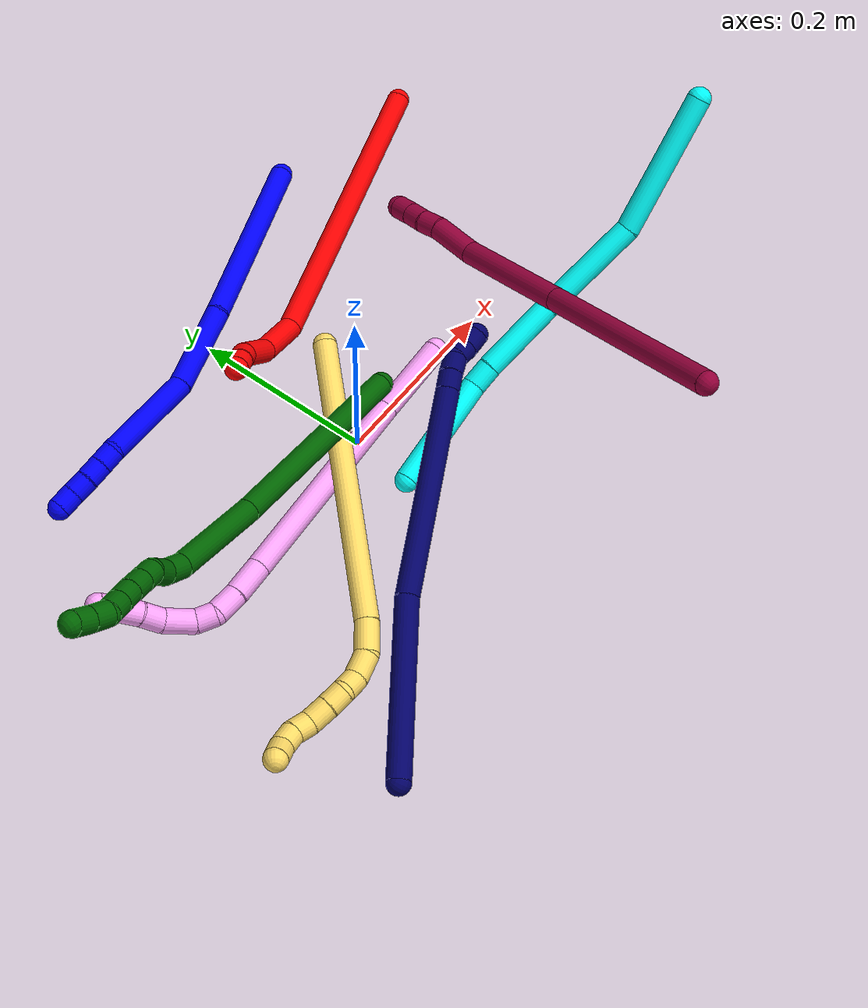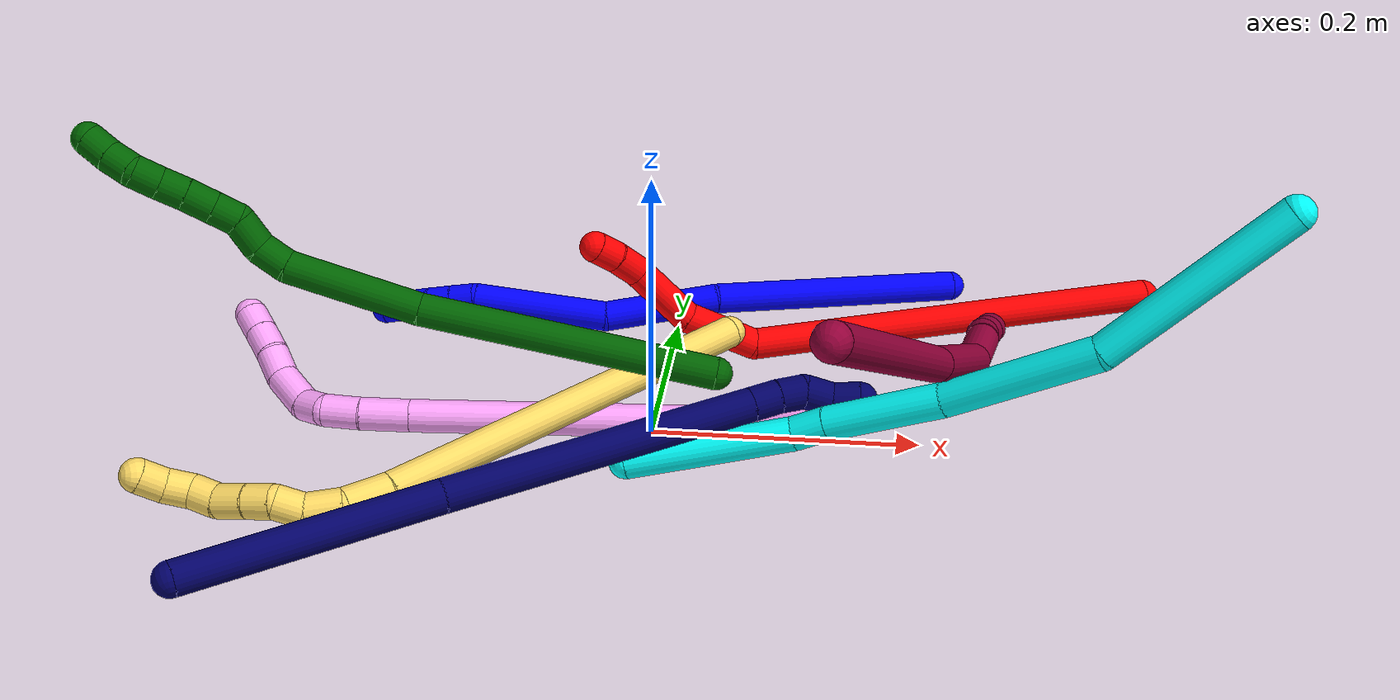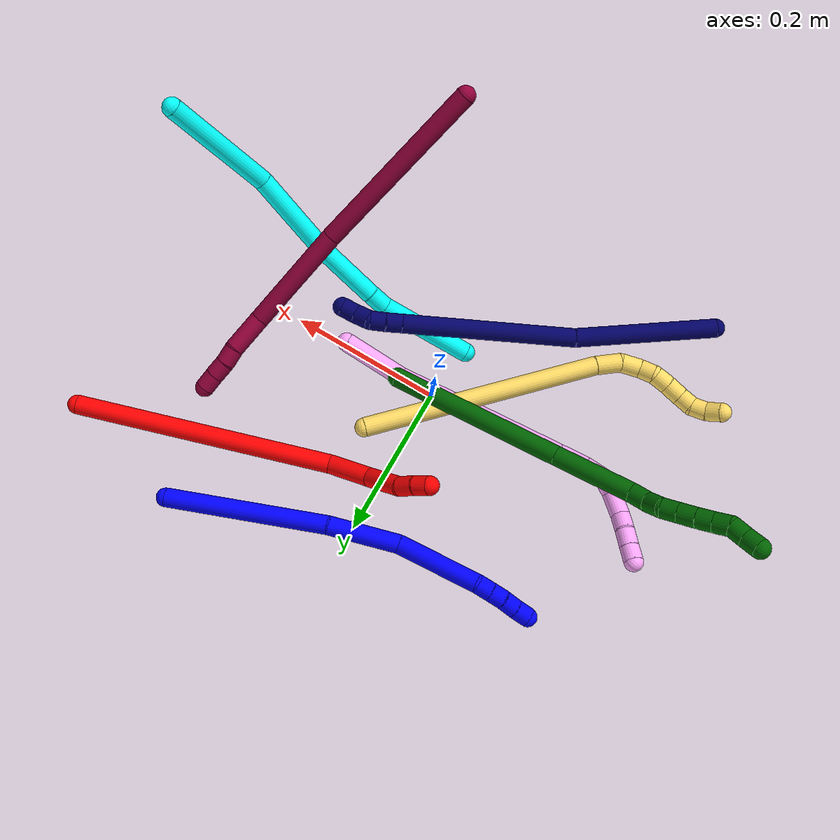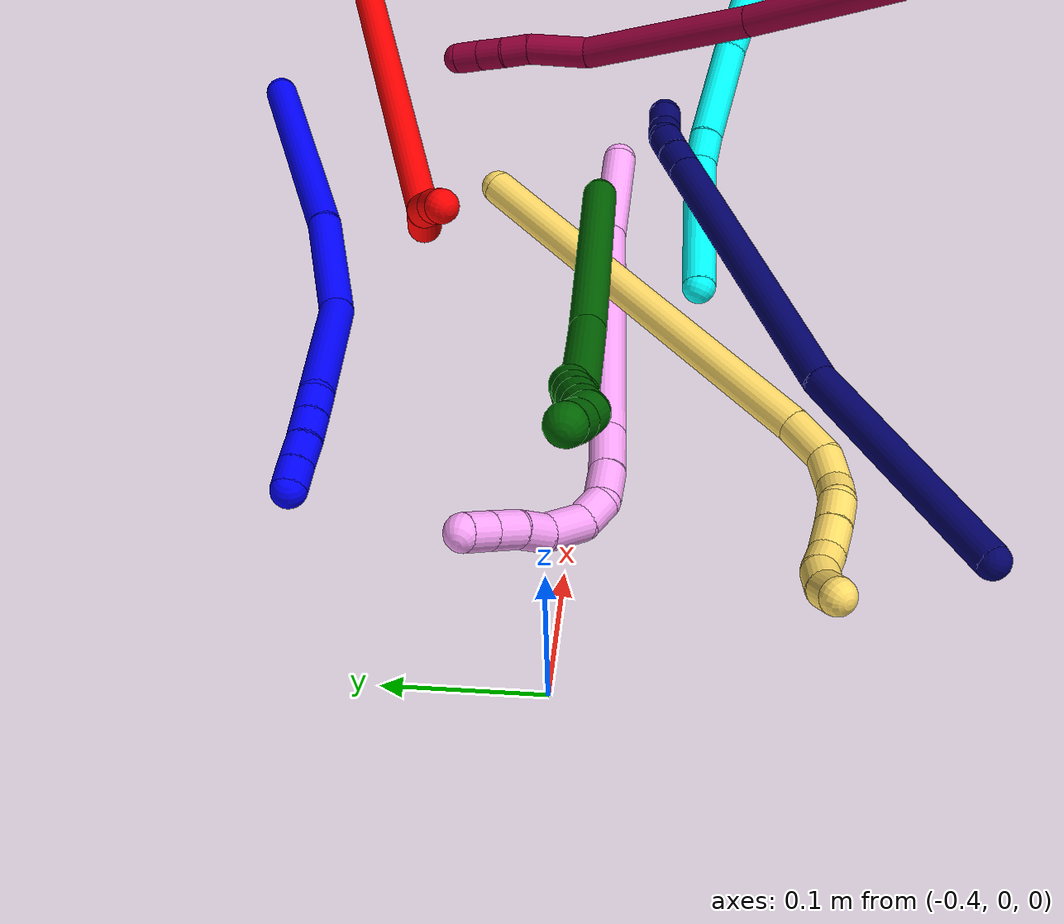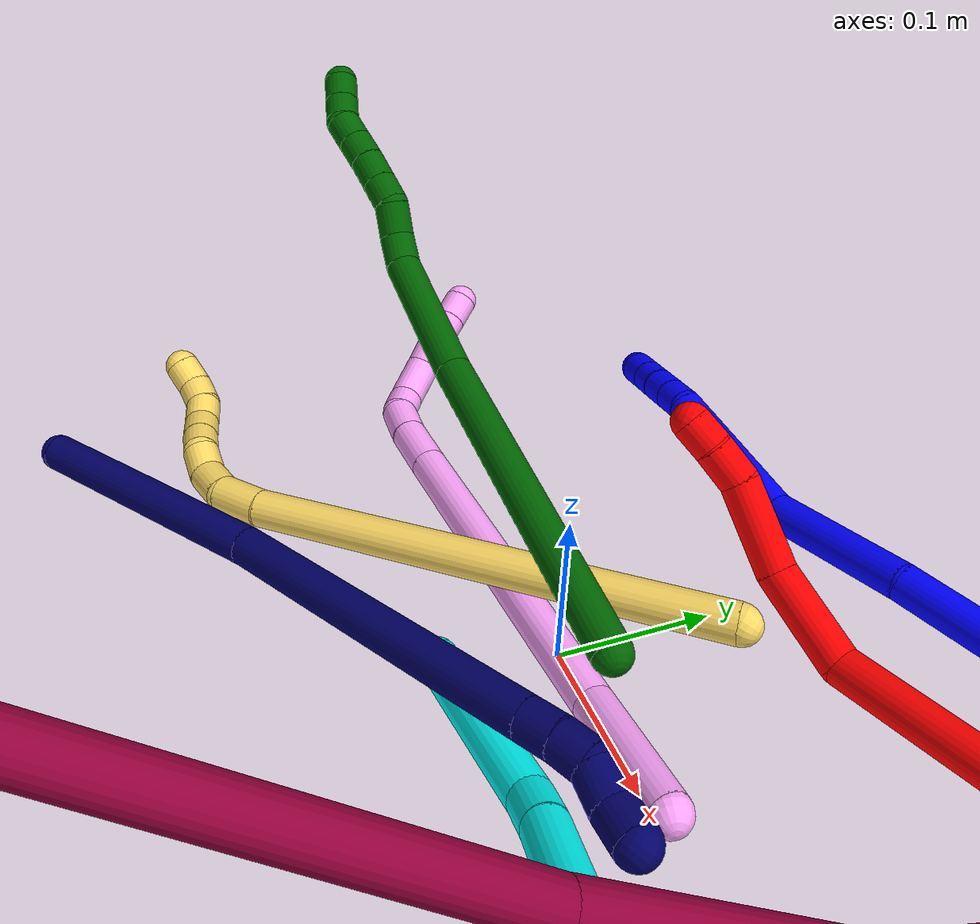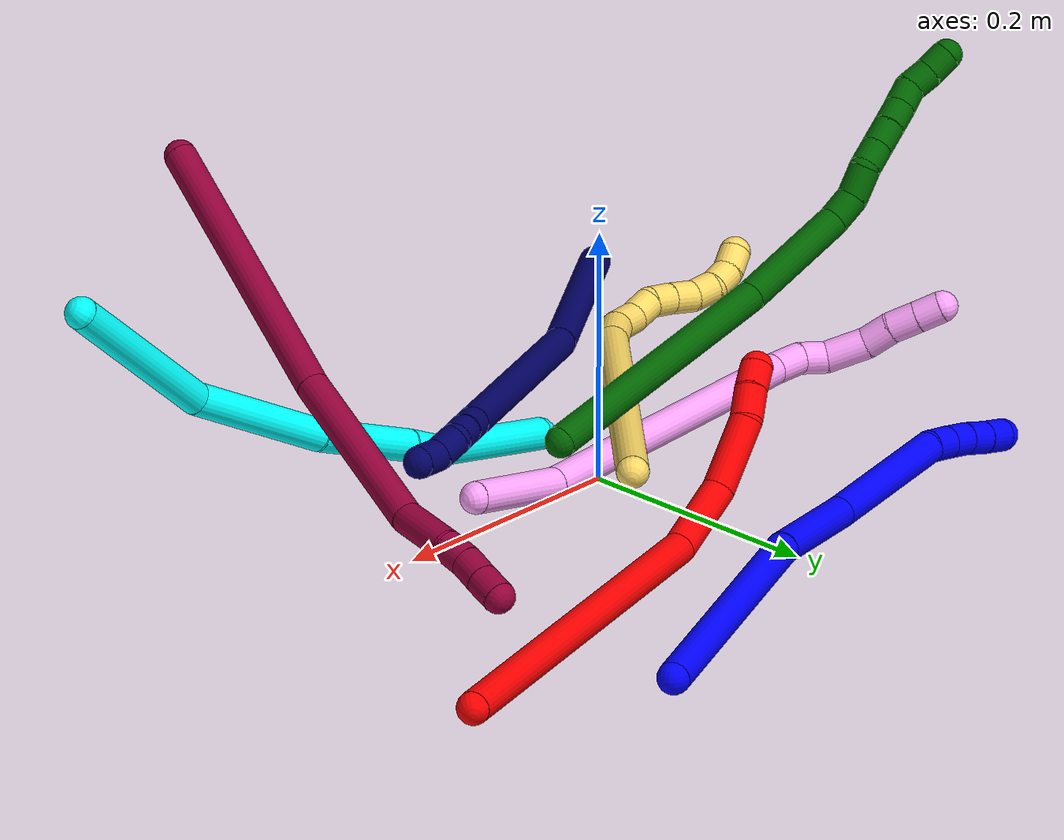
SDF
<sdf version="1.7">
 <world name="default">
  <plugin name="TubeGeneratorPlugin" filename="libtube_generator_plugin.so"/>
  <model name="photoneo_s_sensor">
   <static>1</static>
   <pose>0 0 2 1.57079 1.57079 3.14159</pose>
   <link name="link">
    <inertial><mass>0.1</mass></inertial>
    <sensor name="sensor" type="depth">
     <update_rate>30</update_rate>
     <camera>
      <horizontal_fov>1.22</horizontal_fov>
      <image><width>1920</width><height>1200</height><format>B8G8R8</format></image>
      <clip><near>0.1</near><far>4</far></clip>
      <depth_camera><output>points</output></depth_camera>
     </camera>
     <plugin name="camera_plugin" filename="libgazebo_ros_depth_camera.so">
      <baseline>0.2</baseline>
      <alwaysOn>1</alwaysOn>
      <updateRate>0.0</updateRate>
      <cameraName>camera_ir</cameraName>
      <imageTopicName>/camera/color/image_raw</imageTopicName>
      <cameraInfoTopicName>/camera/color/camera_info</cameraInfoTopicName>
      <depthImageTopicName>/camera/depth/image_raw</depthImageTopicName>
      <depthImageCameraInfoTopicName>/camera/depth/camera_info</depthImageCameraInfoTopicName>
      <pointCloudTopicName>/camera/depth/points</pointCloudTopicName>
      <frameName>fr_optical</frameName>
      <pointCloudCutoff>0.1</pointCloudCutoff>
      <pointCloudCutoffMax>2.0</pointCloudCutoffMax>
      <distortionK1>0</distortionK1>
      <distortionK2>0</distortionK2>
      <distortionK3>0</distortionK3>
      <distortionT1>0</distortionT1>
      <distortionT2>0</distortionT2>
      <CxPrime>0</CxPrime>
      <Cx>0</Cx>
      <Cy>0</Cy>
      <focalLength>0</focalLength>
      <hackBaseline>0</hackBaseline>
     </plugin>
    </sensor>
   </link>
  </model>
  <gravity>0 0 -9.8</gravity>
  <magnetic_field>6e-06 2.3e-05 -4.2e-05</magnetic_field>
  <atmosphere type="adiabatic"/>
  <physics name="default_physics" default="0" type="ode">
   <max_step_size>0.003</max_step_size>
   <real_time_factor>1</real_time_factor>
   <real_time_update_rate>1000</real_time_update_rate>
   <max_contacts>10000</max_contacts>
   <ode>
    <solver>
     <type>quick</type>
     <iters>100</iters>
     <sor>1.3</sor>
     <use_dynamic_moi_rescaling>0</use_dynamic_moi_rescaling>
    </solver>
    <constraints>
     <contact_max_correcting_vel>0</contact_max_correcting_vel>
     <contact_surface_layer>0.001</contact_surface_layer>
     <cfm>0</cfm>
     <erp>0.2</erp>
    </constraints>
   </ode>
  </physics>
  <scene><ambient>0.4 0.4 0.4 1</ambient><background>0.7 0.7 0.7 1</background><shadows>0</shadows></scene>
  <audio><device>default</device></audio>
  <spherical_coordinates>
   <surface_model>EARTH_WGS84</surface_model>
   <latitude_deg>0</latitude_deg>
   <longitude_deg>0</longitude_deg>
   <elevation>0</elevation>
   <heading_deg>0</heading_deg>
  </spherical_coordinates>
  <model name="bin">
   <static>1</static>
   <link name="bottom">
    <collision name="collision-bottom">
     <pose>0 0 -0.01 0 -0 0</pose>
     <geometry><box><size>0.8 0.6 0.02</size></box></geometry>
     <surface>
      <friction><ode><mu>100</mu><mu2>100</mu2></ode></friction>
      <contact><collide_bitmask>65535</collide_bitmask></contact>
     </surface>
    </collision>
   </link>
   <link name="west_wall">
    <collision name="collision-west_wall">
     <pose>-0.41 0 0.1 0 -0 0</pose>
     <geometry><box><size>0.02 0.6 0.2</size></box></geometry>
     <surface>
      <friction><ode><mu>100</mu><mu2>100</mu2></ode></friction>
      <contact><collide_bitmask>65535</collide_bitmask></contact>
     </surface>
    </collision>
   </link>
   <link name="east_wall">
    <collision name="collision-east_wall">
     <pose>0.41 0 0.1 0 -0 0</pose>
     <geometry><box><size>0.02 0.6 0.2</size></box></geometry>
     <surface>
      <friction><ode><mu>100</mu><mu2>100</mu2></ode></friction>
      <contact><collide_bitmask>65535</collide_bitmask></contact>
     </surface>
    </collision>
   </link>
   <link name="south_wall">
    <collision name="collision-south_wall">
     <pose>0 -0.31 0.1 0 -0 0</pose>
     <geometry><box><size>0.8 0.02 0.2</size></box></geometry>
     <surface>
      <friction><ode><mu>100</mu><mu2>100</mu2></ode></friction>
      <contact><collide_bitmask>65535</collide_bitmask></contact>
     </surface>
    </collision>
   </link>
   <link name="north_wall">
    <collision name="collision-north_wall">
     <pose>0 0.31 0.1 0 -0 0</pose>
     <geometry><box><size>0.8 0.02 0.2</size></box></geometry>
     <surface>
      <friction><ode><mu>100</mu><mu2>100</mu2></ode></friction>
      <contact><collide_bitmask>65535</collide_bitmask></contact>
     </surface>
    </collision>
   </link>
  </model>
  <model name="1">
   <static>0</static>
   <link name="1">
    <collision name="collision-cylinder-e_1_1_4">
     <pose>-0.07338 -0.075522 0.017185 1.34705 -0.758405 -0.615771</pose>
     <geometry><cylinder><radius>0.0125</radius><length>0.213388</length></cylinder></geometry>
     <surface>
      <friction><ode><mu>1.16</mu><mu2>1.16</mu2><slip1>0</slip1><slip2>0</slip2></ode></friction>
      <contact><ode><kp>1e+06</kp><kd>1</kd><max_vel>0</max_vel><min_depth>0.001</min_depth></ode></contact>
     </surface>
    </collision>
    <visual name="visual-cylinder-e_1_1_4">
     <pose>-0.07338 -0.075522 0.017185 1.34705 -0.758405 -0.615771</pose>
     <geometry><cylinder><radius>0.0125</radius><length>0.213388</length></cylinder></geometry>
     <material><ambient>0 0 1 1</ambient></material>
    </visual>
    <collision name="collision-cylinder-e_2_4_5">
     <pose>-0.182519 -0.182541 0.034421 1.56919 -0.848681 -0.847477</pose>
     <geometry><cylinder><radius>0.0125</radius><length>0.095305</length></cylinder></geometry>
     <surface>
      <friction><ode><mu>1.16</mu><mu2>1.16</mu2><slip1>0</slip1><slip2>0</slip2></ode></friction>
      <contact><ode><kp>1e+06</kp><kd>1</kd><max_vel>0</max_vel><min_depth>0.001</min_depth></ode></contact>
     </surface>
    </collision>
    <visual name="visual-cylinder-e_2_4_5">
     <pose>-0.182519 -0.182541 0.034421 1.56919 -0.848681 -0.847477</pose>
     <geometry><cylinder><radius>0.0125</radius><length>0.095305</length></cylinder></geometry>
     <material><ambient>0 0 1 1</ambient></material>
    </visual>
    <collision name="collision-cylinder-e_3_5_6">
     <pose>-0.266033 -0.239893 0.046618 1.13162 -1.03172 -0.691356</pose>
     <geometry><cylinder><radius>0.0125</radius><length>0.111293</length></cylinder></geometry>
     <surface>
      <friction><ode><mu>1.16</mu><mu2>1.16</mu2><slip1>0</slip1><slip2>0</slip2></ode></friction>
      <contact><ode><kp>1e+06</kp><kd>1</kd><max_vel>0</max_vel><min_depth>0.001</min_depth></ode></contact>
     </surface>
    </collision>
    <visual name="visual-cylinder-e_3_5_6">
     <pose>-0.266033 -0.239893 0.046618 1.13162 -1.03172 -0.691356</pose>
     <geometry><cylinder><radius>0.0125</radius><length>0.111293</length></cylinder></geometry>
     <material><ambient>0 0 1 1</ambient></material>
    </visual>
    <collision name="collision-cylinder-e_4_6_7">
     <pose>-0.322775 -0.270073 0.058021 1.74065 -1.11652 -1.27512</pose>
     <geometry><cylinder><radius>0.0125</radius><length>0.020003</length></cylinder></geometry>
     <surface>
      <friction><ode><mu>1.16</mu><mu2>1.16</mu2><slip1>0</slip1><slip2>0</slip2></ode></friction>
      <contact><ode><kp>1e+06</kp><kd>1</kd><max_vel>0</max_vel><min_depth>0.001</min_depth></ode></contact>
     </surface>
    </collision>
    <visual name="visual-cylinder-e_4_6_7">
     <pose>-0.322775 -0.270073 0.058021 1.74065 -1.11652 -1.27512</pose>
     <geometry><cylinder><radius>0.0125</radius><length>0.020003</length></cylinder></geometry>
     <material><ambient>0 0 1 1</ambient></material>
    </visual>
    <collision name="collision-cylinder-e_5_7_8">
     <pose>-0.340807 -0.278574 0.056358 1.78807 -1.12924 -1.33536</pose>
     <geometry><cylinder><radius>0.0125</radius><length>0.020009</length></cylinder></geometry>
     <surface>
      <friction><ode><mu>1.16</mu><mu2>1.16</mu2><slip1>0</slip1><slip2>0</slip2></ode></friction>
      <contact><ode><kp>1e+06</kp><kd>1</kd><max_vel>0</max_vel><min_depth>0.001</min_depth></ode></contact>
     </surface>
    </collision>
    <visual name="visual-cylinder-e_5_7_8">
     <pose>-0.340807 -0.278574 0.056358 1.78807 -1.12924 -1.33536</pose>
     <geometry><cylinder><radius>0.0125</radius><length>0.020009</length></cylinder></geometry>
     <material><ambient>0 0 1 1</ambient></material>
    </visual>
    <collision name="collision-cylinder-e_6_8_9">
     <pose>-0.359065 -0.286251 0.053744 2.02101 -1.17127 -1.6264</pose>
     <geometry><cylinder><radius>0.0125</radius><length>0.020001</length></cylinder></geometry>
     <surface>
      <friction><ode><mu>1.16</mu><mu2>1.16</mu2><slip1>0</slip1><slip2>0</slip2></ode></friction>
      <contact><ode><kp>1e+06</kp><kd>1</kd><max_vel>0</max_vel><min_depth>0.001</min_depth></ode></contact>
     </surface>
    </collision>
    <visual name="visual-cylinder-e_6_8_9">
     <pose>-0.359065 -0.286251 0.053744 2.02101 -1.17127 -1.6264</pose>
     <geometry><cylinder><radius>0.0125</radius><length>0.020001</length></cylinder></geometry>
     <material><ambient>0 0 1 1</ambient></material>
    </visual>
    <collision name="collision-cylinder-e_7_9_2">
     <pose>-0.377398 -0.293667 0.050816 1.87656 -1.14797 -1.44575</pose>
     <geometry><cylinder><radius>0.0125</radius><length>0.020002</length></cylinder></geometry>
     <surface>
      <friction><ode><mu>1.16</mu><mu2>1.16</mu2><slip1>0</slip1><slip2>0</slip2></ode></friction>
      <contact><ode><kp>1e+06</kp><kd>1</kd><max_vel>0</max_vel><min_depth>0.001</min_depth></ode></contact>
     </surface>
    </collision>
    <visual name="visual-cylinder-e_7_9_2">
     <pose>-0.377398 -0.293667 0.050816 1.87656 -1.14797 -1.44575</pose>
     <geometry><cylinder><radius>0.0125</radius><length>0.020002</length></cylinder></geometry>
     <material><ambient>0 0 1 1</ambient></material>
    </visual>
    <collision name="collision-sphere-2">
     <pose>-0.386518 -0.29758 0.04958 0 -0 0</pose>
     <geometry><sphere><radius>0.0125</radius></sphere></geometry>
     <surface>
      <friction><ode><mu>1.16</mu><mu2>1.16</mu2><slip1>0</slip1><slip2>0</slip2></ode></friction>
      <contact><ode><kp>1e+06</kp><kd>1</kd><max_vel>0</max_vel><min_depth>0.001</min_depth></ode></contact>
     </surface>
    </collision>
    <visual name="visual-sphere-2">
     <pose>-0.386518 -0.29758 0.04958 0 -0 0</pose>
     <geometry><sphere><radius>0.0125</radius></sphere></geometry>
     <material><ambient>0 0 1 1</ambient></material>
    </visual>
    <collision name="collision-sphere-9">
     <pose>-0.368278 -0.289753 0.052051 0 -0 0</pose>
     <geometry><sphere><radius>0.0125</radius></sphere></geometry>
     <surface>
      <friction><ode><mu>1.16</mu><mu2>1.16</mu2><slip1>0</slip1><slip2>0</slip2></ode></friction>
      <contact><ode><kp>1e+06</kp><kd>1</kd><max_vel>0</max_vel><min_depth>0.001</min_depth></ode></contact>
     </surface>
    </collision>
    <visual name="visual-sphere-9">
     <pose>-0.368278 -0.289753 0.052051 0 -0 0</pose>
     <geometry><sphere><radius>0.0125</radius></sphere></geometry>
     <material><ambient>0 0 1 1</ambient></material>
    </visual>
    <collision name="collision-sphere-4">
     <pose>-0.146761 -0.151044 0.034371 0 -0 0</pose>
     <geometry><sphere><radius>0.0125</radius></sphere></geometry>
     <surface>
      <friction><ode><mu>1.16</mu><mu2>1.16</mu2><slip1>0</slip1><slip2>0</slip2></ode></friction>
      <contact><ode><kp>1e+06</kp><kd>1</kd><max_vel>0</max_vel><min_depth>0.001</min_depth></ode></contact>
     </surface>
    </collision>
    <visual name="visual-sphere-4">
     <pose>-0.146761 -0.151044 0.034371 0 -0 0</pose>
     <geometry><sphere><radius>0.0125</radius></sphere></geometry>
     <material><ambient>0 0 1 1</ambient></material>
    </visual>
    <collision name="collision-sphere-1">
     <geometry><sphere><radius>0.0125</radius></sphere></geometry>
     <surface>
      <friction><ode><mu>1.16</mu><mu2>1.16</mu2><slip1>0</slip1><slip2>0</slip2></ode></friction>
      <contact><ode><kp>1e+06</kp><kd>1</kd><max_vel>0</max_vel><min_depth>0.001</min_depth></ode></contact>
     </surface>
    </collision>
    <visual name="visual-sphere-1">
     <geometry><sphere><radius>0.0125</radius></sphere></geometry>
     <material><ambient>0 0 1 1</ambient></material>
    </visual>
    <collision name="collision-sphere-8">
     <pose>-0.349852 -0.282748 0.055436 0 -0 0</pose>
     <geometry><sphere><radius>0.0125</radius></sphere></geometry>
     <surface>
      <friction><ode><mu>1.16</mu><mu2>1.16</mu2><slip1>0</slip1><slip2>0</slip2></ode></friction>
      <contact><ode><kp>1e+06</kp><kd>1</kd><max_vel>0</max_vel><min_depth>0.001</min_depth></ode></contact>
     </surface>
    </collision>
    <visual name="visual-sphere-8">
     <pose>-0.349852 -0.282748 0.055436 0 -0 0</pose>
     <geometry><sphere><radius>0.0125</radius></sphere></geometry>
     <material><ambient>0 0 1 1</ambient></material>
    </visual>
    <collision name="collision-sphere-5">
     <pose>-0.218278 -0.214038 0.034472 0 -0 0</pose>
     <geometry><sphere><radius>0.0125</radius></sphere></geometry>
     <surface>
      <friction><ode><mu>1.16</mu><mu2>1.16</mu2><slip1>0</slip1><slip2>0</slip2></ode></friction>
      <contact><ode><kp>1e+06</kp><kd>1</kd><max_vel>0</max_vel><min_depth>0.001</min_depth></ode></contact>
     </surface>
    </collision>
    <visual name="visual-sphere-5">
     <pose>-0.218278 -0.214038 0.034472 0 -0 0</pose>
     <geometry><sphere><radius>0.0125</radius></sphere></geometry>
     <material><ambient>0 0 1 1</ambient></material>
    </visual>
    <collision name="collision-sphere-6">
     <pose>-0.313788 -0.265748 0.058763 0 -0 0</pose>
     <geometry><sphere><radius>0.0125</radius></sphere></geometry>
     <surface>
      <friction><ode><mu>1.16</mu><mu2>1.16</mu2><slip1>0</slip1><slip2>0</slip2></ode></friction>
      <contact><ode><kp>1e+06</kp><kd>1</kd><max_vel>0</max_vel><min_depth>0.001</min_depth></ode></contact>
     </surface>
    </collision>
    <visual name="visual-sphere-6">
     <pose>-0.313788 -0.265748 0.058763 0 -0 0</pose>
     <geometry><sphere><radius>0.0125</radius></sphere></geometry>
     <material><ambient>0 0 1 1</ambient></material>
    </visual>
    <collision name="collision-sphere-7">
     <pose>-0.331762 -0.274399 0.05728 0 -0 0</pose>
     <geometry><sphere><radius>0.0125</radius></sphere></geometry>
     <surface>
      <friction><ode><mu>1.16</mu><mu2>1.16</mu2><slip1>0</slip1><slip2>0</slip2></ode></friction>
      <contact><ode><kp>1e+06</kp><kd>1</kd><max_vel>0</max_vel><min_depth>0.001</min_depth></ode></contact>
     </surface>
    </collision>
    <visual name="visual-sphere-7">
     <pose>-0.331762 -0.274399 0.05728 0 -0 0</pose>
     <geometry><sphere><radius>0.0125</radius></sphere></geometry>
     <material><ambient>0 0 1 1</ambient></material>
    </visual>
    <inertial>
     <pose>-0.181334 -0.165573 0.033031 0 -0 0</pose>
     <mass>0.5</mass>
     <inertia>
      <ixx>0.000113</ixx>
      <ixy>0</ixy>
      <ixz>0</ixz>
      <iyy>0.000165</iyy>
      <iyz>0</iyz>
      <izz>0.001418</izz>
     </inertia>
    </inertial>
   </link>
   <pose>0.229805 0.288501 0.011862 0.143446 -0.017795 -0.44871</pose>
  </model>
  <model name="2">
   <static>0</static>
   <link name="2">
    <collision name="collision-cylinder-e_1_1_4">
     <pose>-0.047929 0.07023 -0.145277 -2.6913 -0.288726 1.13114</pose>
     <geometry><cylinder><radius>0.0125</radius><length>0.336659</length></cylinder></geometry>
     <surface>
      <friction><ode><mu>1.16</mu><mu2>1.16</mu2><slip1>0</slip1><slip2>0</slip2></ode></friction>
      <contact><ode><kp>1e+06</kp><kd>1</kd><max_vel>0</max_vel><min_depth>0.001</min_depth></ode></contact>
     </surface>
    </collision>
    <visual name="visual-cylinder-e_1_1_4">
     <pose>-0.047929 0.07023 -0.145277 -2.6913 -0.288726 1.13114</pose>
     <geometry><cylinder><radius>0.0125</radius><length>0.336659</length></cylinder></geometry>
     <material><ambient>1 0 0 1</ambient></material>
    </visual>
    <collision name="collision-cylinder-e_2_4_5">
     <pose>-0.112304 0.140346 -0.316128 3.13714 -0.57149 -3.12645</pose>
     <geometry><cylinder><radius>0.0125</radius><length>0.060812</length></cylinder></geometry>
     <surface>
      <friction><ode><mu>1.16</mu><mu2>1.16</mu2><slip1>0</slip1><slip2>0</slip2></ode></friction>
      <contact><ode><kp>1e+06</kp><kd>1</kd><max_vel>0</max_vel><min_depth>0.001</min_depth></ode></contact>
     </surface>
    </collision>
    <visual name="visual-cylinder-e_2_4_5">
     <pose>-0.112304 0.140346 -0.316128 3.13714 -0.57149 -3.12645</pose>
     <geometry><cylinder><radius>0.0125</radius><length>0.060812</length></cylinder></geometry>
     <material><ambient>1 0 0 1</ambient></material>
    </visual>
    <collision name="collision-cylinder-e_3_5_6">
     <pose>-0.145373 0.130089 -0.362737 2.69229 -0.618623 -1.90008</pose>
     <geometry><cylinder><radius>0.0125</radius><length>0.05733</length></cylinder></geometry>
     <surface>
      <friction><ode><mu>1.16</mu><mu2>1.16</mu2><slip1>0</slip1><slip2>0</slip2></ode></friction>
      <contact><ode><kp>1e+06</kp><kd>1</kd><max_vel>0</max_vel><min_depth>0.001</min_depth></ode></contact>
     </surface>
    </collision>
    <visual name="visual-cylinder-e_3_5_6">
     <pose>-0.145373 0.130089 -0.362737 2.69229 -0.618623 -1.90008</pose>
     <geometry><cylinder><radius>0.0125</radius><length>0.05733</length></cylinder></geometry>
     <material><ambient>1 0 0 1</ambient></material>
    </visual>
    <collision name="collision-cylinder-e_4_6_7">
     <pose>-0.166071 0.115694 -0.394764 2.77242 -0.332878 -1.46534</pose>
     <geometry><cylinder><radius>0.0125</radius><length>0.024939</length></cylinder></geometry>
     <surface>
      <friction><ode><mu>1.16</mu><mu2>1.16</mu2><slip1>0</slip1><slip2>0</slip2></ode></friction>
      <contact><ode><kp>1e+06</kp><kd>1</kd><max_vel>0</max_vel><min_depth>0.001</min_depth></ode></contact>
     </surface>
    </collision>
    <visual name="visual-cylinder-e_4_6_7">
     <pose>-0.166071 0.115694 -0.394764 2.77242 -0.332878 -1.46534</pose>
     <geometry><cylinder><radius>0.0125</radius><length>0.024939</length></cylinder></geometry>
     <material><ambient>1 0 0 1</ambient></material>
    </visual>
    <collision name="collision-cylinder-e_5_7_2">
     <pose>-0.17367 0.109309 -0.415009 2.91513 -0.355331 -2.01245</pose>
     <geometry><cylinder><radius>0.0125</radius><length>0.02026</length></cylinder></geometry>
     <surface>
      <friction><ode><mu>1.16</mu><mu2>1.16</mu2><slip1>0</slip1><slip2>0</slip2></ode></friction>
      <contact><ode><kp>1e+06</kp><kd>1</kd><max_vel>0</max_vel><min_depth>0.001</min_depth></ode></contact>
     </surface>
    </collision>
    <visual name="visual-cylinder-e_5_7_2">
     <pose>-0.17367 0.109309 -0.415009 2.91513 -0.355331 -2.01245</pose>
     <geometry><cylinder><radius>0.0125</radius><length>0.02026</length></cylinder></geometry>
     <material><ambient>1 0 0 1</ambient></material>
    </visual>
    <collision name="collision-sphere-2">
     <pose>-0.177194 0.107176 -0.424264 0 -0 0</pose>
     <geometry><sphere><radius>0.0125</radius></sphere></geometry>
     <surface>
      <friction><ode><mu>1.16</mu><mu2>1.16</mu2><slip1>0</slip1><slip2>0</slip2></ode></friction>
      <contact><ode><kp>1e+06</kp><kd>1</kd><max_vel>0</max_vel><min_depth>0.001</min_depth></ode></contact>
     </surface>
    </collision>
    <visual name="visual-sphere-2">
     <pose>-0.177194 0.107176 -0.424264 0 -0 0</pose>
     <geometry><sphere><radius>0.0125</radius></sphere></geometry>
     <material><ambient>1 0 0 1</ambient></material>
    </visual>
    <collision name="collision-sphere-7">
     <pose>-0.170146 0.111441 -0.405755 0 -0 0</pose>
     <geometry><sphere><radius>0.0125</radius></sphere></geometry>
     <surface>
      <friction><ode><mu>1.16</mu><mu2>1.16</mu2><slip1>0</slip1><slip2>0</slip2></ode></friction>
      <contact><ode><kp>1e+06</kp><kd>1</kd><max_vel>0</max_vel><min_depth>0.001</min_depth></ode></contact>
     </surface>
    </collision>
    <visual name="visual-sphere-7">
     <pose>-0.170146 0.111441 -0.405755 0 -0 0</pose>
     <geometry><sphere><radius>0.0125</radius></sphere></geometry>
     <material><ambient>1 0 0 1</ambient></material>
    </visual>
    <collision name="collision-sphere-6">
     <pose>-0.161996 0.119946 -0.383773 0 -0 0</pose>
     <geometry><sphere><radius>0.0125</radius></sphere></geometry>
     <surface>
      <friction><ode><mu>1.16</mu><mu2>1.16</mu2><slip1>0</slip1><slip2>0</slip2></ode></friction>
      <contact><ode><kp>1e+06</kp><kd>1</kd><max_vel>0</max_vel><min_depth>0.001</min_depth></ode></contact>
     </surface>
    </collision>
    <visual name="visual-sphere-6">
     <pose>-0.161996 0.119946 -0.383773 0 -0 0</pose>
     <geometry><sphere><radius>0.0125</radius></sphere></geometry>
     <material><ambient>1 0 0 1</ambient></material>
    </visual>
    <collision name="collision-sphere-5">
     <pose>-0.12875 0.140232 -0.341702 0 -0 0</pose>
     <geometry><sphere><radius>0.0125</radius></sphere></geometry>
     <surface>
      <friction><ode><mu>1.16</mu><mu2>1.16</mu2><slip1>0</slip1><slip2>0</slip2></ode></friction>
      <contact><ode><kp>1e+06</kp><kd>1</kd><max_vel>0</max_vel><min_depth>0.001</min_depth></ode></contact>
     </surface>
    </collision>
    <visual name="visual-sphere-5">
     <pose>-0.12875 0.140232 -0.341702 0 -0 0</pose>
     <geometry><sphere><radius>0.0125</radius></sphere></geometry>
     <material><ambient>1 0 0 1</ambient></material>
    </visual>
    <collision name="collision-sphere-1">
     <geometry><sphere><radius>0.0125</radius></sphere></geometry>
     <surface>
      <friction><ode><mu>1.16</mu><mu2>1.16</mu2><slip1>0</slip1><slip2>0</slip2></ode></friction>
      <contact><ode><kp>1e+06</kp><kd>1</kd><max_vel>0</max_vel><min_depth>0.001</min_depth></ode></contact>
     </surface>
    </collision>
    <visual name="visual-sphere-1">
     <geometry><sphere><radius>0.0125</radius></sphere></geometry>
     <material><ambient>1 0 0 1</ambient></material>
    </visual>
    <collision name="collision-sphere-4">
     <pose>-0.095857 0.14046 -0.290554 0 -0 0</pose>
     <geometry><sphere><radius>0.0125</radius></sphere></geometry>
     <surface>
      <friction><ode><mu>1.16</mu><mu2>1.16</mu2><slip1>0</slip1><slip2>0</slip2></ode></friction>
      <contact><ode><kp>1e+06</kp><kd>1</kd><max_vel>0</max_vel><min_depth>0.001</min_depth></ode></contact>
     </surface>
    </collision>
    <visual name="visual-sphere-4">
     <pose>-0.095857 0.14046 -0.290554 0 -0 0</pose>
     <geometry><sphere><radius>0.0125</radius></sphere></geometry>
     <material><ambient>1 0 0 1</ambient></material>
    </visual>
    <inertial>
     <pose>-0.077919 0.089472 -0.214364 0 -0 0</pose>
     <mass>0.5</mass>
     <inertia>
      <ixx>0.004018</ixx>
      <ixy>0</ixy>
      <ixz>0</ixz>
      <iyy>0.001926</iyy>
      <iyz>0</iyz>
      <izz>-0.000426</izz>
     </inertia>
    </inertial>
   </link>
   <pose>0.388502 0.243383 0.029476 -1.81866 0.443798 -0.923253</pose>
  </model>
  <model name="3">
   <static>0</static>
   <link name="3">
    <collision name="collision-cylinder-e_1_1_4">
     <pose>-0.000241 -0.023126 -0.071357 2.82818 -0.003211 -0.020323</pose>
     <geometry><cylinder><radius>0.0125</radius><length>0.150022</length></cylinder></geometry>
     <surface>
      <friction><ode><mu>1.16</mu><mu2>1.16</mu2><slip1>0</slip1><slip2>0</slip2></ode></friction>
      <contact><ode><kp>1e+06</kp><kd>1</kd><max_vel>0</max_vel><min_depth>0.001</min_depth></ode></contact>
     </surface>
    </collision>
    <visual name="visual-cylinder-e_1_1_4">
     <pose>-0.000241 -0.023126 -0.071357 2.82818 -0.003211 -0.020323</pose>
     <geometry><cylinder><radius>0.0125</radius><length>0.150022</length></cylinder></geometry>
     <material><ambient>0.003922 1 0.996078 1</ambient></material>
    </visual>
    <collision name="collision-cylinder-e_2_4_5">
     <pose>-0.011422 -0.047608 -0.199377 3.11767 -0.190681 -2.89268</pose>
     <geometry><cylinder><radius>0.0125</radius><length>0.115451</length></cylinder></geometry>
     <surface>
      <friction><ode><mu>1.16</mu><mu2>1.16</mu2><slip1>0</slip1><slip2>0</slip2></ode></friction>
      <contact><ode><kp>1e+06</kp><kd>1</kd><max_vel>0</max_vel><min_depth>0.001</min_depth></ode></contact>
     </surface>
    </collision>
    <visual name="visual-cylinder-e_2_4_5">
     <pose>-0.011422 -0.047608 -0.199377 3.11767 -0.190681 -2.89268</pose>
     <geometry><cylinder><radius>0.0125</radius><length>0.115451</length></cylinder></geometry>
     <material><ambient>0.003922 1 0.996078 1</ambient></material>
    </visual>
    <collision name="collision-cylinder-e_3_5_6">
     <pose>-0.036616 -0.051373 -0.296524 3.08216 -0.337964 -2.79658</pose>
     <geometry><cylinder><radius>0.0125</radius><length>0.085975</length></cylinder></geometry>
     <surface>
      <friction><ode><mu>1.16</mu><mu2>1.16</mu2><slip1>0</slip1><slip2>0</slip2></ode></friction>
      <contact><ode><kp>1e+06</kp><kd>1</kd><max_vel>0</max_vel><min_depth>0.001</min_depth></ode></contact>
     </surface>
    </collision>
    <visual name="visual-cylinder-e_3_5_6">
     <pose>-0.036616 -0.051373 -0.296524 3.08216 -0.337964 -2.79658</pose>
     <geometry><cylinder><radius>0.0125</radius><length>0.085975</length></cylinder></geometry>
     <material><ambient>0.003922 1 0.996078 1</ambient></material>
    </visual>
    <collision name="collision-cylinder-e_4_6_7">
     <pose>-0.054334 -0.055383 -0.349259 3.01167 -0.273398 -2.2581</pose>
     <geometry><cylinder><radius>0.0125</radius><length>0.025663</length></cylinder></geometry>
     <surface>
      <friction><ode><mu>1.16</mu><mu2>1.16</mu2><slip1>0</slip1><slip2>0</slip2></ode></friction>
      <contact><ode><kp>1e+06</kp><kd>1</kd><max_vel>0</max_vel><min_depth>0.001</min_depth></ode></contact>
     </surface>
    </collision>
    <visual name="visual-cylinder-e_4_6_7">
     <pose>-0.054334 -0.055383 -0.349259 3.01167 -0.273398 -2.2581</pose>
     <geometry><cylinder><radius>0.0125</radius><length>0.025663</length></cylinder></geometry>
     <material><ambient>0.003922 1 0.996078 1</ambient></material>
    </visual>
    <collision name="collision-cylinder-e_5_7_2">
     <pose>-0.088678 -0.069729 -0.413079 2.89929 -0.526554 -2.29307</pose>
     <geometry><cylinder><radius>0.0125</radius><length>0.122889</length></cylinder></geometry>
     <surface>
      <friction><ode><mu>1.16</mu><mu2>1.16</mu2><slip1>0</slip1><slip2>0</slip2></ode></friction>
      <contact><ode><kp>1e+06</kp><kd>1</kd><max_vel>0</max_vel><min_depth>0.001</min_depth></ode></contact>
     </surface>
    </collision>
    <visual name="visual-cylinder-e_5_7_2">
     <pose>-0.088678 -0.069729 -0.413079 2.89929 -0.526554 -2.29307</pose>
     <geometry><cylinder><radius>0.0125</radius><length>0.122889</length></cylinder></geometry>
     <material><ambient>0.003922 1 0.996078 1</ambient></material>
    </visual>
    <collision name="collision-sphere-2">
     <pose>-0.119557 -0.082475 -0.464649 0 -0 0</pose>
     <geometry><sphere><radius>0.0125</radius></sphere></geometry>
     <surface>
      <friction><ode><mu>1.16</mu><mu2>1.16</mu2><slip1>0</slip1><slip2>0</slip2></ode></friction>
      <contact><ode><kp>1e+06</kp><kd>1</kd><max_vel>0</max_vel><min_depth>0.001</min_depth></ode></contact>
     </surface>
    </collision>
    <visual name="visual-sphere-2">
     <pose>-0.119557 -0.082475 -0.464649 0 -0 0</pose>
     <geometry><sphere><radius>0.0125</radius></sphere></geometry>
     <material><ambient>0.003922 1 0.996078 1</ambient></material>
    </visual>
    <collision name="collision-sphere-7">
     <pose>-0.057798 -0.056983 -0.36151 0 -0 0</pose>
     <geometry><sphere><radius>0.0125</radius></sphere></geometry>
     <surface>
      <friction><ode><mu>1.16</mu><mu2>1.16</mu2><slip1>0</slip1><slip2>0</slip2></ode></friction>
      <contact><ode><kp>1e+06</kp><kd>1</kd><max_vel>0</max_vel><min_depth>0.001</min_depth></ode></contact>
     </surface>
    </collision>
    <visual name="visual-sphere-7">
     <pose>-0.057798 -0.056983 -0.36151 0 -0 0</pose>
     <geometry><sphere><radius>0.0125</radius></sphere></geometry>
     <material><ambient>0.003922 1 0.996078 1</ambient></material>
    </visual>
    <collision name="collision-sphere-6">
     <pose>-0.050869 -0.053782 -0.337008 0 -0 0</pose>
     <geometry><sphere><radius>0.0125</radius></sphere></geometry>
     <surface>
      <friction><ode><mu>1.16</mu><mu2>1.16</mu2><slip1>0</slip1><slip2>0</slip2></ode></friction>
      <contact><ode><kp>1e+06</kp><kd>1</kd><max_vel>0</max_vel><min_depth>0.001</min_depth></ode></contact>
     </surface>
    </collision>
    <visual name="visual-sphere-6">
     <pose>-0.050869 -0.053782 -0.337008 0 -0 0</pose>
     <geometry><sphere><radius>0.0125</radius></sphere></geometry>
     <material><ambient>0.003922 1 0.996078 1</ambient></material>
    </visual>
    <collision name="collision-sphere-5">
     <pose>-0.022363 -0.048964 -0.25604 0 -0 0</pose>
     <geometry><sphere><radius>0.0125</radius></sphere></geometry>
     <surface>
      <friction><ode><mu>1.16</mu><mu2>1.16</mu2><slip1>0</slip1><slip2>0</slip2></ode></friction>
      <contact><ode><kp>1e+06</kp><kd>1</kd><max_vel>0</max_vel><min_depth>0.001</min_depth></ode></contact>
     </surface>
    </collision>
    <visual name="visual-sphere-5">
     <pose>-0.022363 -0.048964 -0.25604 0 -0 0</pose>
     <geometry><sphere><radius>0.0125</radius></sphere></geometry>
     <material><ambient>0.003922 1 0.996078 1</ambient></material>
    </visual>
    <collision name="collision-sphere-1">
     <geometry><sphere><radius>0.0125</radius></sphere></geometry>
     <surface>
      <friction><ode><mu>1.16</mu><mu2>1.16</mu2><slip1>0</slip1><slip2>0</slip2></ode></friction>
      <contact><ode><kp>1e+06</kp><kd>1</kd><max_vel>0</max_vel><min_depth>0.001</min_depth></ode></contact>
     </surface>
    </collision>
    <visual name="visual-sphere-1">
     <geometry><sphere><radius>0.0125</radius></sphere></geometry>
     <material><ambient>0.003922 1 0.996078 1</ambient></material>
    </visual>
    <collision name="collision-sphere-4">
     <pose>-0.000482 -0.046252 -0.142714 0 -0 0</pose>
     <geometry><sphere><radius>0.0125</radius></sphere></geometry>
     <surface>
      <friction><ode><mu>1.16</mu><mu2>1.16</mu2><slip1>0</slip1><slip2>0</slip2></ode></friction>
      <contact><ode><kp>1e+06</kp><kd>1</kd><max_vel>0</max_vel><min_depth>0.001</min_depth></ode></contact>
     </surface>
    </collision>
    <visual name="visual-sphere-4">
     <pose>-0.000482 -0.046252 -0.142714 0 -0 0</pose>
     <geometry><sphere><radius>0.0125</radius></sphere></geometry>
     <material><ambient>0.003922 1 0.996078 1</ambient></material>
    </visual>
    <inertial>
     <pose>-0.03359 -0.046746 -0.237886 0 -0 0</pose>
     <mass>0.5</mass>
     <inertia>
      <ixx>-0.000152</ixx>
      <ixy>0</ixy>
      <ixz>0</ixz>
      <iyy>-0.00014</iyy>
      <iyz>0</iyz>
      <izz>0.000217</izz>
     </inertia>
    </inertial>
   </link>
   <pose>0.420119 -0.11472 0.234319 0.55339 0.792483 0.314697</pose>
  </model>
  <model name="4">
   <static>0</static>
   <link name="4">
    <collision name="collision-cylinder-e_1_1_4">
     <pose>-0.010444 0.00587 0.040193 -0.145026 -0.25167 0.018378</pose>
     <geometry><cylinder><radius>0.0125</radius><length>0.083882</length></cylinder></geometry>
     <surface>
      <friction><ode><mu>1.16</mu><mu2>1.16</mu2><slip1>0</slip1><slip2>0</slip2></ode></friction>
      <contact><ode><kp>1e+06</kp><kd>1</kd><max_vel>0</max_vel><min_depth>0.001</min_depth></ode></contact>
     </surface>
    </collision>
    <visual name="visual-cylinder-e_1_1_4">
     <pose>-0.010444 0.00587 0.040193 -0.145026 -0.25167 0.018378</pose>
     <geometry><cylinder><radius>0.0125</radius><length>0.083882</length></cylinder></geometry>
     <material><ambient>1 0.65098 0.996078 1</ambient></material>
    </visual>
    <collision name="collision-cylinder-e_2_4_5">
     <pose>-0.051831 0.003885 0.190348 0.07132 -0.273641 -0.009824</pose>
     <geometry><cylinder><radius>0.0125</radius><length>0.229004</length></cylinder></geometry>
     <surface>
      <friction><ode><mu>1.16</mu><mu2>1.16</mu2><slip1>0</slip1><slip2>0</slip2></ode></friction>
      <contact><ode><kp>1e+06</kp><kd>1</kd><max_vel>0</max_vel><min_depth>0.001</min_depth></ode></contact>
     </surface>
    </collision>
    <visual name="visual-cylinder-e_2_4_5">
     <pose>-0.051831 0.003885 0.190348 0.07132 -0.273641 -0.009824</pose>
     <geometry><cylinder><radius>0.0125</radius><length>0.229004</length></cylinder></geometry>
     <material><ambient>1 0.65098 0.996078 1</ambient></material>
    </visual>
    <collision name="collision-cylinder-e_3_5_6">
     <pose>-0.08763 -0.005558 0.318303 0.087952 -0.262611 -0.011623</pose>
     <geometry><cylinder><radius>0.0125</radius><length>0.037407</length></cylinder></geometry>
     <surface>
      <friction><ode><mu>1.16</mu><mu2>1.16</mu2><slip1>0</slip1><slip2>0</slip2></ode></friction>
      <contact><ode><kp>1e+06</kp><kd>1</kd><max_vel>0</max_vel><min_depth>0.001</min_depth></ode></contact>
     </surface>
    </collision>
    <visual name="visual-cylinder-e_3_5_6">
     <pose>-0.08763 -0.005558 0.318303 0.087952 -0.262611 -0.011623</pose>
     <geometry><cylinder><radius>0.0125</radius><length>0.037407</length></cylinder></geometry>
     <material><ambient>1 0.65098 0.996078 1</ambient></material>
    </visual>
    <collision name="collision-cylinder-e_4_6_7">
     <pose>-0.094687 -0.007768 0.350234 0.044754 -0.156491 -0.00351</pose>
     <geometry><cylinder><radius>0.0125</radius><length>0.028251</length></cylinder></geometry>
     <surface>
      <friction><ode><mu>1.16</mu><mu2>1.16</mu2><slip1>0</slip1><slip2>0</slip2></ode></friction>
      <contact><ode><kp>1e+06</kp><kd>1</kd><max_vel>0</max_vel><min_depth>0.001</min_depth></ode></contact>
     </surface>
    </collision>
    <visual name="visual-cylinder-e_4_6_7">
     <pose>-0.094687 -0.007768 0.350234 0.044754 -0.156491 -0.00351</pose>
     <geometry><cylinder><radius>0.0125</radius><length>0.028251</length></cylinder></geometry>
     <material><ambient>1 0.65098 0.996078 1</ambient></material>
    </visual>
    <collision name="collision-cylinder-e_5_7_8">
     <pose>-0.094052 -0.005924 0.374203 -0.241285 0.267961 -0.032678</pose>
     <geometry><cylinder><radius>0.0125</radius><length>0.021425</length></cylinder></geometry>
     <surface>
      <friction><ode><mu>1.16</mu><mu2>1.16</mu2><slip1>0</slip1><slip2>0</slip2></ode></friction>
      <contact><ode><kp>1e+06</kp><kd>1</kd><max_vel>0</max_vel><min_depth>0.001</min_depth></ode></contact>
     </surface>
    </collision>
    <visual name="visual-cylinder-e_5_7_8">
     <pose>-0.094052 -0.005924 0.374203 -0.241285 0.267961 -0.032678</pose>
     <geometry><cylinder><radius>0.0125</radius><length>0.021425</length></cylinder></geometry>
     <material><ambient>1 0.65098 0.996078 1</ambient></material>
    </visual>
    <collision name="collision-cylinder-e_6_8_9">
     <pose>-0.081644 -0.005326 0.39804 0.134638 0.601956 0.04185</pose>
     <geometry><cylinder><radius>0.0125</radius><length>0.033805</length></cylinder></geometry>
     <surface>
      <friction><ode><mu>1.16</mu><mu2>1.16</mu2><slip1>0</slip1><slip2>0</slip2></ode></friction>
      <contact><ode><kp>1e+06</kp><kd>1</kd><max_vel>0</max_vel><min_depth>0.001</min_depth></ode></contact>
     </surface>
    </collision>
    <visual name="visual-cylinder-e_6_8_9">
     <pose>-0.081644 -0.005326 0.39804 0.134638 0.601956 0.04185</pose>
     <geometry><cylinder><radius>0.0125</radius><length>0.033805</length></cylinder></geometry>
     <material><ambient>1 0.65098 0.996078 1</ambient></material>
    </visual>
    <collision name="collision-cylinder-e_7_9_10">
     <pose>-0.064168 -0.011121 0.419311 0.484017 0.753011 0.194573</pose>
     <geometry><cylinder><radius>0.0125</radius><length>0.02312</length></cylinder></geometry>
     <surface>
      <friction><ode><mu>1.16</mu><mu2>1.16</mu2><slip1>0</slip1><slip2>0</slip2></ode></friction>
      <contact><ode><kp>1e+06</kp><kd>1</kd><max_vel>0</max_vel><min_depth>0.001</min_depth></ode></contact>
     </surface>
    </collision>
    <visual name="visual-cylinder-e_7_9_10">
     <pose>-0.064168 -0.011121 0.419311 0.484017 0.753011 0.194573</pose>
     <geometry><cylinder><radius>0.0125</radius><length>0.02312</length></cylinder></geometry>
     <material><ambient>1 0.65098 0.996078 1</ambient></material>
    </visual>
    <collision name="collision-cylinder-e_8_10_11">
     <pose>-0.048537 -0.017091 0.434908 0.246443 0.744553 0.096647</pose>
     <geometry><cylinder><radius>0.0125</radius><length>0.022801</length></cylinder></geometry>
     <surface>
      <friction><ode><mu>1.16</mu><mu2>1.16</mu2><slip1>0</slip1><slip2>0</slip2></ode></friction>
      <contact><ode><kp>1e+06</kp><kd>1</kd><max_vel>0</max_vel><min_depth>0.001</min_depth></ode></contact>
     </surface>
    </collision>
    <visual name="visual-cylinder-e_8_10_11">
     <pose>-0.048537 -0.017091 0.434908 0.246443 0.744553 0.096647</pose>
     <geometry><cylinder><radius>0.0125</radius><length>0.022801</length></cylinder></geometry>
     <material><ambient>1 0.65098 0.996078 1</ambient></material>
    </visual>
    <collision name="collision-cylinder-e_9_11_2">
     <pose>-0.034076 -0.021043 0.450391 0.253713 0.725386 0.096723</pose>
     <geometry><cylinder><radius>0.0125</radius><length>0.020304</length></cylinder></geometry>
     <surface>
      <friction><ode><mu>1.16</mu><mu2>1.16</mu2><slip1>0</slip1><slip2>0</slip2></ode></friction>
      <contact><ode><kp>1e+06</kp><kd>1</kd><max_vel>0</max_vel><min_depth>0.001</min_depth></ode></contact>
     </surface>
    </collision>
    <visual name="visual-cylinder-e_9_11_2">
     <pose>-0.034076 -0.021043 0.450391 0.253713 0.725386 0.096723</pose>
     <geometry><cylinder><radius>0.0125</radius><length>0.020304</length></cylinder></geometry>
     <material><ambient>1 0.65098 0.996078 1</ambient></material>
    </visual>
    <collision name="collision-sphere-2">
     <pose>-0.027341 -0.02295 0.457744 0 -0 0</pose>
     <geometry><sphere><radius>0.0125</radius></sphere></geometry>
     <surface>
      <friction><ode><mu>1.16</mu><mu2>1.16</mu2><slip1>0</slip1><slip2>0</slip2></ode></friction>
      <contact><ode><kp>1e+06</kp><kd>1</kd><max_vel>0</max_vel><min_depth>0.001</min_depth></ode></contact>
     </surface>
    </collision>
    <visual name="visual-sphere-2">
     <pose>-0.027341 -0.02295 0.457744 0 -0 0</pose>
     <geometry><sphere><radius>0.0125</radius></sphere></geometry>
     <material><ambient>1 0.65098 0.996078 1</ambient></material>
    </visual>
    <collision name="collision-sphere-11">
     <pose>-0.040811 -0.019137 0.443038 0 -0 0</pose>
     <geometry><sphere><radius>0.0125</radius></sphere></geometry>
     <surface>
      <friction><ode><mu>1.16</mu><mu2>1.16</mu2><slip1>0</slip1><slip2>0</slip2></ode></friction>
      <contact><ode><kp>1e+06</kp><kd>1</kd><max_vel>0</max_vel><min_depth>0.001</min_depth></ode></contact>
     </surface>
    </collision>
    <visual name="visual-sphere-11">
     <pose>-0.040811 -0.019137 0.443038 0 -0 0</pose>
     <geometry><sphere><radius>0.0125</radius></sphere></geometry>
     <material><ambient>1 0.65098 0.996078 1</ambient></material>
    </visual>
    <collision name="collision-sphere-10">
     <pose>-0.056263 -0.015046 0.426777 0 -0 0</pose>
     <geometry><sphere><radius>0.0125</radius></sphere></geometry>
     <surface>
      <friction><ode><mu>1.16</mu><mu2>1.16</mu2><slip1>0</slip1><slip2>0</slip2></ode></friction>
      <contact><ode><kp>1e+06</kp><kd>1</kd><max_vel>0</max_vel><min_depth>0.001</min_depth></ode></contact>
     </surface>
    </collision>
    <visual name="visual-sphere-10">
     <pose>-0.056263 -0.015046 0.426777 0 -0 0</pose>
     <geometry><sphere><radius>0.0125</radius></sphere></geometry>
     <material><ambient>1 0.65098 0.996078 1</ambient></material>
    </visual>
    <collision name="collision-sphere-9">
     <pose>-0.072073 -0.007196 0.411846 0 -0 0</pose>
     <geometry><sphere><radius>0.0125</radius></sphere></geometry>
     <surface>
      <friction><ode><mu>1.16</mu><mu2>1.16</mu2><slip1>0</slip1><slip2>0</slip2></ode></friction>
      <contact><ode><kp>1e+06</kp><kd>1</kd><max_vel>0</max_vel><min_depth>0.001</min_depth></ode></contact>
     </surface>
    </collision>
    <visual name="visual-sphere-9">
     <pose>-0.072073 -0.007196 0.411846 0 -0 0</pose>
     <geometry><sphere><radius>0.0125</radius></sphere></geometry>
     <material><ambient>1 0.65098 0.996078 1</ambient></material>
    </visual>
    <collision name="collision-sphere-4">
     <pose>-0.020888 0.011741 0.080387 0 -0 0</pose>
     <geometry><sphere><radius>0.0125</radius></sphere></geometry>
     <surface>
      <friction><ode><mu>1.16</mu><mu2>1.16</mu2><slip1>0</slip1><slip2>0</slip2></ode></friction>
      <contact><ode><kp>1e+06</kp><kd>1</kd><max_vel>0</max_vel><min_depth>0.001</min_depth></ode></contact>
     </surface>
    </collision>
    <visual name="visual-sphere-4">
     <pose>-0.020888 0.011741 0.080387 0 -0 0</pose>
     <geometry><sphere><radius>0.0125</radius></sphere></geometry>
     <material><ambient>1 0.65098 0.996078 1</ambient></material>
    </visual>
    <collision name="collision-sphere-1">
     <geometry><sphere><radius>0.0125</radius></sphere></geometry>
     <surface>
      <friction><ode><mu>1.16</mu><mu2>1.16</mu2><slip1>0</slip1><slip2>0</slip2></ode></friction>
      <contact><ode><kp>1e+06</kp><kd>1</kd><max_vel>0</max_vel><min_depth>0.001</min_depth></ode></contact>
     </surface>
    </collision>
    <visual name="visual-sphere-1">
     <geometry><sphere><radius>0.0125</radius></sphere></geometry>
     <material><ambient>1 0.65098 0.996078 1</ambient></material>
    </visual>
    <collision name="collision-sphere-8">
     <pose>-0.091216 -0.003456 0.384234 0 -0 0</pose>
     <geometry><sphere><radius>0.0125</radius></sphere></geometry>
     <surface>
      <friction><ode><mu>1.16</mu><mu2>1.16</mu2><slip1>0</slip1><slip2>0</slip2></ode></friction>
      <contact><ode><kp>1e+06</kp><kd>1</kd><max_vel>0</max_vel><min_depth>0.001</min_depth></ode></contact>
     </surface>
    </collision>
    <visual name="visual-sphere-8">
     <pose>-0.091216 -0.003456 0.384234 0 -0 0</pose>
     <geometry><sphere><radius>0.0125</radius></sphere></geometry>
     <material><ambient>1 0.65098 0.996078 1</ambient></material>
    </visual>
    <collision name="collision-sphere-5">
     <pose>-0.082774 -0.003971 0.30031 0 -0 0</pose>
     <geometry><sphere><radius>0.0125</radius></sphere></geometry>
     <surface>
      <friction><ode><mu>1.16</mu><mu2>1.16</mu2><slip1>0</slip1><slip2>0</slip2></ode></friction>
      <contact><ode><kp>1e+06</kp><kd>1</kd><max_vel>0</max_vel><min_depth>0.001</min_depth></ode></contact>
     </surface>
    </collision>
    <visual name="visual-sphere-5">
     <pose>-0.082774 -0.003971 0.30031 0 -0 0</pose>
     <geometry><sphere><radius>0.0125</radius></sphere></geometry>
     <material><ambient>1 0.65098 0.996078 1</ambient></material>
    </visual>
    <collision name="collision-sphere-6">
     <pose>-0.092485 -0.007144 0.336295 0 -0 0</pose>
     <geometry><sphere><radius>0.0125</radius></sphere></geometry>
     <surface>
      <friction><ode><mu>1.16</mu><mu2>1.16</mu2><slip1>0</slip1><slip2>0</slip2></ode></friction>
      <contact><ode><kp>1e+06</kp><kd>1</kd><max_vel>0</max_vel><min_depth>0.001</min_depth></ode></contact>
     </surface>
    </collision>
    <visual name="visual-sphere-6">
     <pose>-0.092485 -0.007144 0.336295 0 -0 0</pose>
     <geometry><sphere><radius>0.0125</radius></sphere></geometry>
     <material><ambient>1 0.65098 0.996078 1</ambient></material>
    </visual>
    <collision name="collision-sphere-7">
     <pose>-0.096888 -0.008393 0.364173 0 -0 0</pose>
     <geometry><sphere><radius>0.0125</radius></sphere></geometry>
     <surface>
      <friction><ode><mu>1.16</mu><mu2>1.16</mu2><slip1>0</slip1><slip2>0</slip2></ode></friction>
      <contact><ode><kp>1e+06</kp><kd>1</kd><max_vel>0</max_vel><min_depth>0.001</min_depth></ode></contact>
     </surface>
    </collision>
    <visual name="visual-sphere-7">
     <pose>-0.096888 -0.008393 0.364173 0 -0 0</pose>
     <geometry><sphere><radius>0.0125</radius></sphere></geometry>
     <material><ambient>1 0.65098 0.996078 1</ambient></material>
    </visual>
    <inertial>
     <pose>-0.053512 -0.000853 0.237984 0 -0 0</pose>
     <mass>0.5</mass>
     <inertia>
      <ixx>0.00103</ixx>
      <ixy>0</ixy>
      <ixz>0</ixz>
      <iyy>0.001069</iyy>
      <iyz>0</iyz>
      <izz>0.000381</izz>
     </inertia>
    </inertial>
   </link>
   <pose>0.129547 -0.003022 0.026843 -1.52989 -0.36509 1.34838</pose>
  </model>
  <model name="5">
   <static>0</static>
   <link name="5">
    <collision name="collision-cylinder-e_1_1_4">
     <pose>-0.041084 -0.036061 0.147326 0.240053 -0.26452 -0.032087</pose>
     <geometry><cylinder><radius>0.0125</radius><length>0.314282</length></cylinder></geometry>
     <surface>
      <friction><ode><mu>1.16</mu><mu2>1.16</mu2><slip1>0</slip1><slip2>0</slip2></ode></friction>
      <contact><ode><kp>1e+06</kp><kd>1</kd><max_vel>0</max_vel><min_depth>0.001</min_depth></ode></contact>
     </surface>
    </collision>
    <visual name="visual-cylinder-e_1_1_4">
     <pose>-0.041084 -0.036061 0.147326 0.240053 -0.26452 -0.032087</pose>
     <geometry><cylinder><radius>0.0125</radius><length>0.314282</length></cylinder></geometry>
     <material><ambient>1 0.858824 0.4 1</ambient></material>
    </visual>
    <collision name="collision-cylinder-e_2_4_5">
     <pose>-0.087092 -0.073641 0.310829 0.093565 -0.294264 -0.013876</pose>
     <geometry><cylinder><radius>0.0125</radius><length>0.033956</length></cylinder></geometry>
     <surface>
      <friction><ode><mu>1.16</mu><mu2>1.16</mu2><slip1>0</slip1><slip2>0</slip2></ode></friction>
      <contact><ode><kp>1e+06</kp><kd>1</kd><max_vel>0</max_vel><min_depth>0.001</min_depth></ode></contact>
     </surface>
    </collision>
    <visual name="visual-cylinder-e_2_4_5">
     <pose>-0.087092 -0.073641 0.310829 0.093565 -0.294264 -0.013876</pose>
     <geometry><cylinder><radius>0.0125</radius><length>0.033956</length></cylinder></geometry>
     <material><ambient>1 0.858824 0.4 1</ambient></material>
    </visual>
    <collision name="collision-cylinder-e_3_5_6">
     <pose>-0.097602 -0.071286 0.338679 -0.32034 -0.426302 0.069905</pose>
     <geometry><cylinder><radius>0.0125</radius><length>0.027016</length></cylinder></geometry>
     <surface>
      <friction><ode><mu>1.16</mu><mu2>1.16</mu2><slip1>0</slip1><slip2>0</slip2></ode></friction>
      <contact><ode><kp>1e+06</kp><kd>1</kd><max_vel>0</max_vel><min_depth>0.001</min_depth></ode></contact>
     </surface>
    </collision>
    <visual name="visual-cylinder-e_3_5_6">
     <pose>-0.097602 -0.071286 0.338679 -0.32034 -0.426302 0.069905</pose>
     <geometry><cylinder><radius>0.0125</radius><length>0.027016</length></cylinder></geometry>
     <material><ambient>1 0.858824 0.4 1</ambient></material>
    </visual>
    <collision name="collision-cylinder-e_4_6_7">
     <pose>-0.103933 -0.061533 0.359097 -0.591991 -0.070619 0.021544</pose>
     <geometry><cylinder><radius>0.0125</radius><length>0.021127</length></cylinder></geometry>
     <surface>
      <friction><ode><mu>1.16</mu><mu2>1.16</mu2><slip1>0</slip1><slip2>0</slip2></ode></friction>
      <contact><ode><kp>1e+06</kp><kd>1</kd><max_vel>0</max_vel><min_depth>0.001</min_depth></ode></contact>
     </surface>
    </collision>
    <visual name="visual-cylinder-e_4_6_7">
     <pose>-0.103933 -0.061533 0.359097 -0.591991 -0.070619 0.021544</pose>
     <geometry><cylinder><radius>0.0125</radius><length>0.021127</length></cylinder></geometry>
     <material><ambient>1 0.858824 0.4 1</ambient></material>
    </visual>
    <collision name="collision-cylinder-e_5_7_8">
     <pose>-0.109672 -0.049777 0.374407 -0.730044 -0.515619 0.200849</pose>
     <geometry><cylinder><radius>0.0125</radius><length>0.020256</length></cylinder></geometry>
     <surface>
      <friction><ode><mu>1.16</mu><mu2>1.16</mu2><slip1>0</slip1><slip2>0</slip2></ode></friction>
      <contact><ode><kp>1e+06</kp><kd>1</kd><max_vel>0</max_vel><min_depth>0.001</min_depth></ode></contact>
     </surface>
    </collision>
    <visual name="visual-cylinder-e_5_7_8">
     <pose>-0.109672 -0.049777 0.374407 -0.730044 -0.515619 0.200849</pose>
     <geometry><cylinder><radius>0.0125</radius><length>0.020256</length></cylinder></geometry>
     <material><ambient>1 0.858824 0.4 1</ambient></material>
    </visual>
    <collision name="collision-cylinder-e_6_8_9">
     <pose>-0.120794 -0.036851 0.387889 -0.794939 -0.555348 0.238193</pose>
     <geometry><cylinder><radius>0.0125</radius><length>0.023246</length></cylinder></geometry>
     <surface>
      <friction><ode><mu>1.16</mu><mu2>1.16</mu2><slip1>0</slip1><slip2>0</slip2></ode></friction>
      <contact><ode><kp>1e+06</kp><kd>1</kd><max_vel>0</max_vel><min_depth>0.001</min_depth></ode></contact>
     </surface>
    </collision>
    <visual name="visual-cylinder-e_6_8_9">
     <pose>-0.120794 -0.036851 0.387889 -0.794939 -0.555348 0.238193</pose>
     <geometry><cylinder><radius>0.0125</radius><length>0.023246</length></cylinder></geometry>
     <material><ambient>1 0.858824 0.4 1</ambient></material>
    </visual>
    <collision name="collision-cylinder-e_7_9_10">
     <pose>-0.128969 -0.022302 0.401136 -0.869751 -0.205628 0.095786</pose>
     <geometry><cylinder><radius>0.0125</radius><length>0.020051</length></cylinder></geometry>
     <surface>
      <friction><ode><mu>1.16</mu><mu2>1.16</mu2><slip1>0</slip1><slip2>0</slip2></ode></friction>
      <contact><ode><kp>1e+06</kp><kd>1</kd><max_vel>0</max_vel><min_depth>0.001</min_depth></ode></contact>
     </surface>
    </collision>
    <visual name="visual-cylinder-e_7_9_10">
     <pose>-0.128969 -0.022302 0.401136 -0.869751 -0.205628 0.095786</pose>
     <geometry><cylinder><radius>0.0125</radius><length>0.020051</length></cylinder></geometry>
     <material><ambient>1 0.858824 0.4 1</ambient></material>
    </visual>
    <collision name="collision-cylinder-e_8_10_11">
     <pose>-0.132155 -0.01002 0.416181 -0.501844 -0.114086 0.029273</pose>
     <geometry><cylinder><radius>0.0125</radius><length>0.020011</length></cylinder></geometry>
     <surface>
      <friction><ode><mu>1.16</mu><mu2>1.16</mu2><slip1>0</slip1><slip2>0</slip2></ode></friction>
      <contact><ode><kp>1e+06</kp><kd>1</kd><max_vel>0</max_vel><min_depth>0.001</min_depth></ode></contact>
     </surface>
    </collision>
    <visual name="visual-cylinder-e_8_10_11">
     <pose>-0.132155 -0.01002 0.416181 -0.501844 -0.114086 0.029273</pose>
     <geometry><cylinder><radius>0.0125</radius><length>0.020011</length></cylinder></geometry>
     <material><ambient>1 0.858824 0.4 1</ambient></material>
    </visual>
    <collision name="collision-cylinder-e_9_11_2">
     <pose>-0.131054 -0.002077 0.434145 -0.329354 0.225269 -0.03759</pose>
     <geometry><cylinder><radius>0.0125</radius><length>0.020056</length></cylinder></geometry>
     <surface>
      <friction><ode><mu>1.16</mu><mu2>1.16</mu2><slip1>0</slip1><slip2>0</slip2></ode></friction>
      <contact><ode><kp>1e+06</kp><kd>1</kd><max_vel>0</max_vel><min_depth>0.001</min_depth></ode></contact>
     </surface>
    </collision>
    <visual name="visual-cylinder-e_9_11_2">
     <pose>-0.131054 -0.002077 0.434145 -0.329354 0.225269 -0.03759</pose>
     <geometry><cylinder><radius>0.0125</radius><length>0.020056</length></cylinder></geometry>
     <material><ambient>1 0.858824 0.4 1</ambient></material>
    </visual>
    <collision name="collision-sphere-2">
     <pose>-0.128814 0.001085 0.443394 0 -0 0</pose>
     <geometry><sphere><radius>0.0125</radius></sphere></geometry>
     <surface>
      <friction><ode><mu>1.16</mu><mu2>1.16</mu2><slip1>0</slip1><slip2>0</slip2></ode></friction>
      <contact><ode><kp>1e+06</kp><kd>1</kd><max_vel>0</max_vel><min_depth>0.001</min_depth></ode></contact>
     </surface>
    </collision>
    <visual name="visual-sphere-2">
     <pose>-0.128814 0.001085 0.443394 0 -0 0</pose>
     <geometry><sphere><radius>0.0125</radius></sphere></geometry>
     <material><ambient>1 0.858824 0.4 1</ambient></material>
    </visual>
    <collision name="collision-sphere-11">
     <pose>-0.133294 -0.005238 0.424895 0 -0 0</pose>
     <geometry><sphere><radius>0.0125</radius></sphere></geometry>
     <surface>
      <friction><ode><mu>1.16</mu><mu2>1.16</mu2><slip1>0</slip1><slip2>0</slip2></ode></friction>
      <contact><ode><kp>1e+06</kp><kd>1</kd><max_vel>0</max_vel><min_depth>0.001</min_depth></ode></contact>
     </surface>
    </collision>
    <visual name="visual-sphere-11">
     <pose>-0.133294 -0.005238 0.424895 0 -0 0</pose>
     <geometry><sphere><radius>0.0125</radius></sphere></geometry>
     <material><ambient>1 0.858824 0.4 1</ambient></material>
    </visual>
    <collision name="collision-sphere-10">
     <pose>-0.131016 -0.014802 0.407466 0 -0 0</pose>
     <geometry><sphere><radius>0.0125</radius></sphere></geometry>
     <surface>
      <friction><ode><mu>1.16</mu><mu2>1.16</mu2><slip1>0</slip1><slip2>0</slip2></ode></friction>
      <contact><ode><kp>1e+06</kp><kd>1</kd><max_vel>0</max_vel><min_depth>0.001</min_depth></ode></contact>
     </surface>
    </collision>
    <visual name="visual-sphere-10">
     <pose>-0.131016 -0.014802 0.407466 0 -0 0</pose>
     <geometry><sphere><radius>0.0125</radius></sphere></geometry>
     <material><ambient>1 0.858824 0.4 1</ambient></material>
    </visual>
    <collision name="collision-sphere-9">
     <pose>-0.126922 -0.029801 0.394805 0 -0 0</pose>
     <geometry><sphere><radius>0.0125</radius></sphere></geometry>
     <surface>
      <friction><ode><mu>1.16</mu><mu2>1.16</mu2><slip1>0</slip1><slip2>0</slip2></ode></friction>
      <contact><ode><kp>1e+06</kp><kd>1</kd><max_vel>0</max_vel><min_depth>0.001</min_depth></ode></contact>
     </surface>
    </collision>
    <visual name="visual-sphere-9">
     <pose>-0.126922 -0.029801 0.394805 0 -0 0</pose>
     <geometry><sphere><radius>0.0125</radius></sphere></geometry>
     <material><ambient>1 0.858824 0.4 1</ambient></material>
    </visual>
    <collision name="collision-sphere-4">
     <pose>-0.082168 -0.072123 0.294652 0 -0 0</pose>
     <geometry><sphere><radius>0.0125</radius></sphere></geometry>
     <surface>
      <friction><ode><mu>1.16</mu><mu2>1.16</mu2><slip1>0</slip1><slip2>0</slip2></ode></friction>
      <contact><ode><kp>1e+06</kp><kd>1</kd><max_vel>0</max_vel><min_depth>0.001</min_depth></ode></contact>
     </surface>
    </collision>
    <visual name="visual-sphere-4">
     <pose>-0.082168 -0.072123 0.294652 0 -0 0</pose>
     <geometry><sphere><radius>0.0125</radius></sphere></geometry>
     <material><ambient>1 0.858824 0.4 1</ambient></material>
    </visual>
    <collision name="collision-sphere-1">
     <geometry><sphere><radius>0.0125</radius></sphere></geometry>
     <surface>
      <friction><ode><mu>1.16</mu><mu2>1.16</mu2><slip1>0</slip1><slip2>0</slip2></ode></friction>
      <contact><ode><kp>1e+06</kp><kd>1</kd><max_vel>0</max_vel><min_depth>0.001</min_depth></ode></contact>
     </surface>
    </collision>
    <visual name="visual-sphere-1">
     <geometry><sphere><radius>0.0125</radius></sphere></geometry>
     <material><ambient>1 0.858824 0.4 1</ambient></material>
    </visual>
    <collision name="collision-sphere-8">
     <pose>-0.114666 -0.043901 0.380972 0 -0 0</pose>
     <geometry><sphere><radius>0.0125</radius></sphere></geometry>
     <surface>
      <friction><ode><mu>1.16</mu><mu2>1.16</mu2><slip1>0</slip1><slip2>0</slip2></ode></friction>
      <contact><ode><kp>1e+06</kp><kd>1</kd><max_vel>0</max_vel><min_depth>0.001</min_depth></ode></contact>
     </surface>
    </collision>
    <visual name="visual-sphere-8">
     <pose>-0.114666 -0.043901 0.380972 0 -0 0</pose>
     <geometry><sphere><radius>0.0125</radius></sphere></geometry>
     <material><ambient>1 0.858824 0.4 1</ambient></material>
    </visual>
    <collision name="collision-sphere-5">
     <pose>-0.092016 -0.075159 0.327006 0 -0 0</pose>
     <geometry><sphere><radius>0.0125</radius></sphere></geometry>
     <surface>
      <friction><ode><mu>1.16</mu><mu2>1.16</mu2><slip1>0</slip1><slip2>0</slip2></ode></friction>
      <contact><ode><kp>1e+06</kp><kd>1</kd><max_vel>0</max_vel><min_depth>0.001</min_depth></ode></contact>
     </surface>
    </collision>
    <visual name="visual-sphere-5">
     <pose>-0.092016 -0.075159 0.327006 0 -0 0</pose>
     <geometry><sphere><radius>0.0125</radius></sphere></geometry>
     <material><ambient>1 0.858824 0.4 1</ambient></material>
    </visual>
    <collision name="collision-sphere-6">
     <pose>-0.103187 -0.067413 0.350353 0 -0 0</pose>
     <geometry><sphere><radius>0.0125</radius></sphere></geometry>
     <surface>
      <friction><ode><mu>1.16</mu><mu2>1.16</mu2><slip1>0</slip1><slip2>0</slip2></ode></friction>
      <contact><ode><kp>1e+06</kp><kd>1</kd><max_vel>0</max_vel><min_depth>0.001</min_depth></ode></contact>
     </surface>
    </collision>
    <visual name="visual-sphere-6">
     <pose>-0.103187 -0.067413 0.350353 0 -0 0</pose>
     <geometry><sphere><radius>0.0125</radius></sphere></geometry>
     <material><ambient>1 0.858824 0.4 1</ambient></material>
    </visual>
    <collision name="collision-sphere-7">
     <pose>-0.104678 -0.055653 0.367841 0 -0 0</pose>
     <geometry><sphere><radius>0.0125</radius></sphere></geometry>
     <surface>
      <friction><ode><mu>1.16</mu><mu2>1.16</mu2><slip1>0</slip1><slip2>0</slip2></ode></friction>
      <contact><ode><kp>1e+06</kp><kd>1</kd><max_vel>0</max_vel><min_depth>0.001</min_depth></ode></contact>
     </surface>
    </collision>
    <visual name="visual-sphere-7">
     <pose>-0.104678 -0.055653 0.367841 0 -0 0</pose>
     <geometry><sphere><radius>0.0125</radius></sphere></geometry>
     <material><ambient>1 0.858824 0.4 1</ambient></material>
    </visual>
    <inertial>
     <pose>-0.06718 -0.039228 0.230544 0 -0 0</pose>
     <mass>0.5</mass>
     <inertia>
      <ixx>0.002433</ixx>
      <ixy>0</ixy>
      <ixz>0</ixz>
      <iyy>0.002464</iyy>
      <iyz>0</iyz>
      <izz>0.00131</izz>
     </inertia>
    </inertial>
   </link>
   <pose>0.051463 0.082438 0.048895 0.957792 -1.16488 -0.328761</pose>
  </model>
  <model name="6">
   <static>0</static>
   <link name="6">
    <collision name="collision-cylinder-e_1_1_4">
     <pose>-0.013665 0.008096 0.111513 -0.072472 -0.121613 0.004414</pose>
     <geometry><cylinder><radius>0.0125</radius><length>0.225278</length></cylinder></geometry>
     <surface>
      <friction><ode><mu>1.16</mu><mu2>1.16</mu2><slip1>0</slip1><slip2>0</slip2></ode></friction>
      <contact><ode><kp>1e+06</kp><kd>1</kd><max_vel>0</max_vel><min_depth>0.001</min_depth></ode></contact>
     </surface>
    </collision>
    <visual name="visual-cylinder-e_1_1_4">
     <pose>-0.013665 0.008096 0.111513 -0.072472 -0.121613 0.004414</pose>
     <geometry><cylinder><radius>0.0125</radius><length>0.225278</length></cylinder></geometry>
     <material><ambient>0 0.392157 0.003922 1</ambient></material>
    </visual>
    <collision name="collision-cylinder-e_2_4_5">
     <pose>-0.036998 0.015693 0.273254 0.009933 -0.190159 -0.000947</pose>
     <geometry><cylinder><radius>0.0125</radius><length>0.102304</length></cylinder></geometry>
     <surface>
      <friction><ode><mu>1.16</mu><mu2>1.16</mu2><slip1>0</slip1><slip2>0</slip2></ode></friction>
      <contact><ode><kp>1e+06</kp><kd>1</kd><max_vel>0</max_vel><min_depth>0.001</min_depth></ode></contact>
     </surface>
    </collision>
    <visual name="visual-cylinder-e_2_4_5">
     <pose>-0.036998 0.015693 0.273254 0.009933 -0.190159 -0.000947</pose>
     <geometry><cylinder><radius>0.0125</radius><length>0.102304</length></cylinder></geometry>
     <material><ambient>0 0.392157 0.003922 1</ambient></material>
    </visual>
    <collision name="collision-cylinder-e_3_5_6">
     <pose>-0.050308 0.011875 0.334585 0.290431 -0.304487 -0.044869</pose>
     <geometry><cylinder><radius>0.0125</radius><length>0.024295</length></cylinder></geometry>
     <surface>
      <friction><ode><mu>1.16</mu><mu2>1.16</mu2><slip1>0</slip1><slip2>0</slip2></ode></friction>
      <contact><ode><kp>1e+06</kp><kd>1</kd><max_vel>0</max_vel><min_depth>0.001</min_depth></ode></contact>
     </surface>
    </collision>
    <visual name="visual-cylinder-e_3_5_6">
     <pose>-0.050308 0.011875 0.334585 0.290431 -0.304487 -0.044869</pose>
     <geometry><cylinder><radius>0.0125</radius><length>0.024295</length></cylinder></geometry>
     <material><ambient>0 0.392157 0.003922 1</ambient></material>
    </visual>
    <collision name="collision-cylinder-e_4_6_7">
     <pose>-0.060915 0.00258 0.354415 0.600544 -0.582371 -0.185067</pose>
     <geometry><cylinder><radius>0.0125</radius><length>0.02533</length></cylinder></geometry>
     <surface>
      <friction><ode><mu>1.16</mu><mu2>1.16</mu2><slip1>0</slip1><slip2>0</slip2></ode></friction>
      <contact><ode><kp>1e+06</kp><kd>1</kd><max_vel>0</max_vel><min_depth>0.001</min_depth></ode></contact>
     </surface>
    </collision>
    <visual name="visual-cylinder-e_4_6_7">
     <pose>-0.060915 0.00258 0.354415 0.600544 -0.582371 -0.185067</pose>
     <geometry><cylinder><radius>0.0125</radius><length>0.02533</length></cylinder></geometry>
     <material><ambient>0 0.392157 0.003922 1</ambient></material>
    </visual>
    <collision name="collision-cylinder-e_5_7_8">
     <pose>-0.072363 -0.004051 0.372283 0.071366 -0.45485 -0.016523</pose>
     <geometry><cylinder><radius>0.0125</radius><length>0.020405</length></cylinder></geometry>
     <surface>
      <friction><ode><mu>1.16</mu><mu2>1.16</mu2><slip1>0</slip1><slip2>0</slip2></ode></friction>
      <contact><ode><kp>1e+06</kp><kd>1</kd><max_vel>0</max_vel><min_depth>0.001</min_depth></ode></contact>
     </surface>
    </collision>
    <visual name="visual-cylinder-e_5_7_8">
     <pose>-0.072363 -0.004051 0.372283 0.071366 -0.45485 -0.016523</pose>
     <geometry><cylinder><radius>0.0125</radius><length>0.020405</length></cylinder></geometry>
     <material><ambient>0 0.392157 0.003922 1</ambient></material>
    </visual>
    <collision name="collision-cylinder-e_6_8_9">
     <pose>-0.081649 -0.0054 0.39122 0.070874 -0.454917 -0.016411</pose>
     <geometry><cylinder><radius>0.0125</radius><length>0.021864</length></cylinder></geometry>
     <surface>
      <friction><ode><mu>1.16</mu><mu2>1.16</mu2><slip1>0</slip1><slip2>0</slip2></ode></friction>
      <contact><ode><kp>1e+06</kp><kd>1</kd><max_vel>0</max_vel><min_depth>0.001</min_depth></ode></contact>
     </surface>
    </collision>
    <visual name="visual-cylinder-e_6_8_9">
     <pose>-0.081649 -0.0054 0.39122 0.070874 -0.454917 -0.016411</pose>
     <geometry><cylinder><radius>0.0125</radius><length>0.021864</length></cylinder></geometry>
     <material><ambient>0 0.392157 0.003922 1</ambient></material>
    </visual>
    <collision name="collision-cylinder-e_7_9_10">
     <pose>-0.0908 -0.006216 0.410047 0.013337 -0.448649 -0.003043</pose>
     <geometry><cylinder><radius>0.0125</radius><length>0.020049</length></cylinder></geometry>
     <surface>
      <friction><ode><mu>1.16</mu><mu2>1.16</mu2><slip1>0</slip1><slip2>0</slip2></ode></friction>
      <contact><ode><kp>1e+06</kp><kd>1</kd><max_vel>0</max_vel><min_depth>0.001</min_depth></ode></contact>
     </surface>
    </collision>
    <visual name="visual-cylinder-e_7_9_10">
     <pose>-0.0908 -0.006216 0.410047 0.013337 -0.448649 -0.003043</pose>
     <geometry><cylinder><radius>0.0125</radius><length>0.020049</length></cylinder></geometry>
     <material><ambient>0 0.392157 0.003922 1</ambient></material>
    </visual>
    <collision name="collision-cylinder-e_8_10_11">
     <pose>-0.100018 -0.00664 0.428029 0.033934 -0.498058 -0.008631</pose>
     <geometry><cylinder><radius>0.0125</radius><length>0.020389</length></cylinder></geometry>
     <surface>
      <friction><ode><mu>1.16</mu><mu2>1.16</mu2><slip1>0</slip1><slip2>0</slip2></ode></friction>
      <contact><ode><kp>1e+06</kp><kd>1</kd><max_vel>0</max_vel><min_depth>0.001</min_depth></ode></contact>
     </surface>
    </collision>
    <visual name="visual-cylinder-e_8_10_11">
     <pose>-0.100018 -0.00664 0.428029 0.033934 -0.498058 -0.008631</pose>
     <geometry><cylinder><radius>0.0125</radius><length>0.020389</length></cylinder></geometry>
     <material><ambient>0 0.392157 0.003922 1</ambient></material>
    </visual>
    <collision name="collision-cylinder-e_9_11_12">
     <pose>-0.10606 -0.009958 0.446476 0.307338 -0.116994 -0.018141</pose>
     <geometry><cylinder><radius>0.0125</radius><length>0.020062</length></cylinder></geometry>
     <surface>
      <friction><ode><mu>1.16</mu><mu2>1.16</mu2><slip1>0</slip1><slip2>0</slip2></ode></friction>
      <contact><ode><kp>1e+06</kp><kd>1</kd><max_vel>0</max_vel><min_depth>0.001</min_depth></ode></contact>
     </surface>
    </collision>
    <visual name="visual-cylinder-e_9_11_12">
     <pose>-0.10606 -0.009958 0.446476 0.307338 -0.116994 -0.018141</pose>
     <geometry><cylinder><radius>0.0125</radius><length>0.020062</length></cylinder></geometry>
     <material><ambient>0 0.392157 0.003922 1</ambient></material>
    </visual>
    <collision name="collision-cylinder-e_10_12_2">
     <pose>-0.10936 -0.01671 0.465013 0.392127 -0.214356 -0.042732</pose>
     <geometry><cylinder><radius>0.0125</radius><length>0.020026</length></cylinder></geometry>
     <surface>
      <friction><ode><mu>1.16</mu><mu2>1.16</mu2><slip1>0</slip1><slip2>0</slip2></ode></friction>
      <contact><ode><kp>1e+06</kp><kd>1</kd><max_vel>0</max_vel><min_depth>0.001</min_depth></ode></contact>
     </surface>
    </collision>
    <visual name="visual-cylinder-e_10_12_2">
     <pose>-0.10936 -0.01671 0.465013 0.392127 -0.214356 -0.042732</pose>
     <geometry><cylinder><radius>0.0125</radius><length>0.020026</length></cylinder></geometry>
     <material><ambient>0 0.392157 0.003922 1</ambient></material>
    </visual>
    <collision name="collision-sphere-2">
     <pose>-0.11149 -0.020449 0.474054 0 -0 0</pose>
     <geometry><sphere><radius>0.0125</radius></sphere></geometry>
     <surface>
      <friction><ode><mu>1.16</mu><mu2>1.16</mu2><slip1>0</slip1><slip2>0</slip2></ode></friction>
      <contact><ode><kp>1e+06</kp><kd>1</kd><max_vel>0</max_vel><min_depth>0.001</min_depth></ode></contact>
     </surface>
    </collision>
    <visual name="visual-sphere-2">
     <pose>-0.11149 -0.020449 0.474054 0 -0 0</pose>
     <geometry><sphere><radius>0.0125</radius></sphere></geometry>
     <material><ambient>0 0.392157 0.003922 1</ambient></material>
    </visual>
    <collision name="collision-sphere-12">
     <pose>-0.10723 -0.012972 0.455972 0 -0 0</pose>
     <geometry><sphere><radius>0.0125</radius></sphere></geometry>
     <surface>
      <friction><ode><mu>1.16</mu><mu2>1.16</mu2><slip1>0</slip1><slip2>0</slip2></ode></friction>
      <contact><ode><kp>1e+06</kp><kd>1</kd><max_vel>0</max_vel><min_depth>0.001</min_depth></ode></contact>
     </surface>
    </collision>
    <visual name="visual-sphere-12">
     <pose>-0.10723 -0.012972 0.455972 0 -0 0</pose>
     <geometry><sphere><radius>0.0125</radius></sphere></geometry>
     <material><ambient>0 0.392157 0.003922 1</ambient></material>
    </visual>
    <collision name="collision-sphere-11">
     <pose>-0.104889 -0.006944 0.43698 0 -0 0</pose>
     <geometry><sphere><radius>0.0125</radius></sphere></geometry>
     <surface>
      <friction><ode><mu>1.16</mu><mu2>1.16</mu2><slip1>0</slip1><slip2>0</slip2></ode></friction>
      <contact><ode><kp>1e+06</kp><kd>1</kd><max_vel>0</max_vel><min_depth>0.001</min_depth></ode></contact>
     </surface>
    </collision>
    <visual name="visual-sphere-11">
     <pose>-0.104889 -0.006944 0.43698 0 -0 0</pose>
     <geometry><sphere><radius>0.0125</radius></sphere></geometry>
     <material><ambient>0 0.392157 0.003922 1</ambient></material>
    </visual>
    <collision name="collision-sphere-10">
     <pose>-0.095148 -0.006336 0.419078 0 -0 0</pose>
     <geometry><sphere><radius>0.0125</radius></sphere></geometry>
     <surface>
      <friction><ode><mu>1.16</mu><mu2>1.16</mu2><slip1>0</slip1><slip2>0</slip2></ode></friction>
      <contact><ode><kp>1e+06</kp><kd>1</kd><max_vel>0</max_vel><min_depth>0.001</min_depth></ode></contact>
     </surface>
    </collision>
    <visual name="visual-sphere-10">
     <pose>-0.095148 -0.006336 0.419078 0 -0 0</pose>
     <geometry><sphere><radius>0.0125</radius></sphere></geometry>
     <material><ambient>0 0.392157 0.003922 1</ambient></material>
    </visual>
    <collision name="collision-sphere-9">
     <pose>-0.086452 -0.006095 0.401015 0 -0 0</pose>
     <geometry><sphere><radius>0.0125</radius></sphere></geometry>
     <surface>
      <friction><ode><mu>1.16</mu><mu2>1.16</mu2><slip1>0</slip1><slip2>0</slip2></ode></friction>
      <contact><ode><kp>1e+06</kp><kd>1</kd><max_vel>0</max_vel><min_depth>0.001</min_depth></ode></contact>
     </surface>
    </collision>
    <visual name="visual-sphere-9">
     <pose>-0.086452 -0.006095 0.401015 0 -0 0</pose>
     <geometry><sphere><radius>0.0125</radius></sphere></geometry>
     <material><ambient>0 0.392157 0.003922 1</ambient></material>
    </visual>
    <collision name="collision-sphere-4">
     <pose>-0.027329 0.016192 0.223027 0 -0 0</pose>
     <geometry><sphere><radius>0.0125</radius></sphere></geometry>
     <surface>
      <friction><ode><mu>1.16</mu><mu2>1.16</mu2><slip1>0</slip1><slip2>0</slip2></ode></friction>
      <contact><ode><kp>1e+06</kp><kd>1</kd><max_vel>0</max_vel><min_depth>0.001</min_depth></ode></contact>
     </surface>
    </collision>
    <visual name="visual-sphere-4">
     <pose>-0.027329 0.016192 0.223027 0 -0 0</pose>
     <geometry><sphere><radius>0.0125</radius></sphere></geometry>
     <material><ambient>0 0.392157 0.003922 1</ambient></material>
    </visual>
    <collision name="collision-sphere-1">
     <geometry><sphere><radius>0.0125</radius></sphere></geometry>
     <surface>
      <friction><ode><mu>1.16</mu><mu2>1.16</mu2><slip1>0</slip1><slip2>0</slip2></ode></friction>
      <contact><ode><kp>1e+06</kp><kd>1</kd><max_vel>0</max_vel><min_depth>0.001</min_depth></ode></contact>
     </surface>
    </collision>
    <visual name="visual-sphere-1">
     <geometry><sphere><radius>0.0125</radius></sphere></geometry>
     <material><ambient>0 0.392157 0.003922 1</ambient></material>
    </visual>
    <collision name="collision-sphere-8">
     <pose>-0.076845 -0.004704 0.381424 0 -0 0</pose>
     <geometry><sphere><radius>0.0125</radius></sphere></geometry>
     <surface>
      <friction><ode><mu>1.16</mu><mu2>1.16</mu2><slip1>0</slip1><slip2>0</slip2></ode></friction>
      <contact><ode><kp>1e+06</kp><kd>1</kd><max_vel>0</max_vel><min_depth>0.001</min_depth></ode></contact>
     </surface>
    </collision>
    <visual name="visual-sphere-8">
     <pose>-0.076845 -0.004704 0.381424 0 -0 0</pose>
     <geometry><sphere><radius>0.0125</radius></sphere></geometry>
     <material><ambient>0 0.392157 0.003922 1</ambient></material>
    </visual>
    <collision name="collision-sphere-5">
     <pose>-0.046666 0.015194 0.323482 0 -0 0</pose>
     <geometry><sphere><radius>0.0125</radius></sphere></geometry>
     <surface>
      <friction><ode><mu>1.16</mu><mu2>1.16</mu2><slip1>0</slip1><slip2>0</slip2></ode></friction>
      <contact><ode><kp>1e+06</kp><kd>1</kd><max_vel>0</max_vel><min_depth>0.001</min_depth></ode></contact>
     </surface>
    </collision>
    <visual name="visual-sphere-5">
     <pose>-0.046666 0.015194 0.323482 0 -0 0</pose>
     <geometry><sphere><radius>0.0125</radius></sphere></geometry>
     <material><ambient>0 0.392157 0.003922 1</ambient></material>
    </visual>
    <collision name="collision-sphere-6">
     <pose>-0.05395 0.008557 0.345688 0 -0 0</pose>
     <geometry><sphere><radius>0.0125</radius></sphere></geometry>
     <surface>
      <friction><ode><mu>1.16</mu><mu2>1.16</mu2><slip1>0</slip1><slip2>0</slip2></ode></friction>
      <contact><ode><kp>1e+06</kp><kd>1</kd><max_vel>0</max_vel><min_depth>0.001</min_depth></ode></contact>
     </surface>
    </collision>
    <visual name="visual-sphere-6">
     <pose>-0.05395 0.008557 0.345688 0 -0 0</pose>
     <geometry><sphere><radius>0.0125</radius></sphere></geometry>
     <material><ambient>0 0.392157 0.003922 1</ambient></material>
    </visual>
    <collision name="collision-sphere-7">
     <pose>-0.067881 -0.003397 0.363141 0 -0 0</pose>
     <geometry><sphere><radius>0.0125</radius></sphere></geometry>
     <surface>
      <friction><ode><mu>1.16</mu><mu2>1.16</mu2><slip1>0</slip1><slip2>0</slip2></ode></friction>
      <contact><ode><kp>1e+06</kp><kd>1</kd><max_vel>0</max_vel><min_depth>0.001</min_depth></ode></contact>
     </surface>
    </collision>
    <visual name="visual-sphere-7">
     <pose>-0.067881 -0.003397 0.363141 0 -0 0</pose>
     <geometry><sphere><radius>0.0125</radius></sphere></geometry>
     <material><ambient>0 0.392157 0.003922 1</ambient></material>
    </visual>
    <inertial>
     <pose>-0.042135 0.005576 0.243099 0 -0 0</pose>
     <mass>0.5</mass>
     <inertia>
      <ixx>0.001053</ixx>
      <ixy>0</ixy>
      <ixz>0</ixz>
      <iyy>0.001067</iyy>
      <iyz>0</iyz>
      <izz>0.000111</izz>
     </inertia>
    </inertial>
   </link>
   <pose>0.047483 0.00596 0.048382 -1.33152 0.787697 1.64753</pose>
  </model>
  <model name="7">
   <static>0</static>
   <link name="7">
    <collision name="collision-cylinder-e_1_1_4">
     <pose>0.085614 0.036603 -0.014431 -1.94634 1.14001 -1.51077</pose>
     <geometry><cylinder><radius>0.0125</radius><length>0.188444</length></cylinder></geometry>
     <surface>
      <friction><ode><mu>1.16</mu><mu2>1.16</mu2><slip1>0</slip1><slip2>0</slip2></ode></friction>
      <contact><ode><kp>1e+06</kp><kd>1</kd><max_vel>0</max_vel><min_depth>0.001</min_depth></ode></contact>
     </surface>
    </collision>
    <visual name="visual-cylinder-e_1_1_4">
     <pose>0.085614 0.036603 -0.014431 -1.94634 1.14001 -1.51077</pose>
     <geometry><cylinder><radius>0.0125</radius><length>0.188444</length></cylinder></geometry>
     <material><ambient>0.003922 0 0.403922 1</ambient></material>
    </visual>
    <collision name="collision-cylinder-e_2_4_5">
     <pose>0.26923 0.132023 -0.037076 -1.70956 1.02599 -1.14915</pose>
     <geometry><cylinder><radius>0.0125</radius><length>0.229184</length></cylinder></geometry>
     <surface>
      <friction><ode><mu>1.16</mu><mu2>1.16</mu2><slip1>0</slip1><slip2>0</slip2></ode></friction>
      <contact><ode><kp>1e+06</kp><kd>1</kd><max_vel>0</max_vel><min_depth>0.001</min_depth></ode></contact>
     </surface>
    </collision>
    <visual name="visual-cylinder-e_2_4_5">
     <pose>0.26923 0.132023 -0.037076 -1.70956 1.02599 -1.14915</pose>
     <geometry><cylinder><radius>0.0125</radius><length>0.229184</length></cylinder></geometry>
     <material><ambient>0.003922 0 0.403922 1</ambient></material>
    </visual>
    <collision name="collision-cylinder-e_3_5_6">
     <pose>0.376218 0.196219 -0.046061 -1.71297 1.02688 -1.15324</pose>
     <geometry><cylinder><radius>0.0125</radius><length>0.021001</length></cylinder></geometry>
     <surface>
      <friction><ode><mu>1.16</mu><mu2>1.16</mu2><slip1>0</slip1><slip2>0</slip2></ode></friction>
      <contact><ode><kp>1e+06</kp><kd>1</kd><max_vel>0</max_vel><min_depth>0.001</min_depth></ode></contact>
     </surface>
    </collision>
    <visual name="visual-cylinder-e_3_5_6">
     <pose>0.376218 0.196219 -0.046061 -1.71297 1.02688 -1.15324</pose>
     <geometry><cylinder><radius>0.0125</radius><length>0.021001</length></cylinder></geometry>
     <material><ambient>0.003922 0 0.403922 1</ambient></material>
    </visual>
    <collision name="collision-cylinder-e_4_6_7">
     <pose>0.393967 0.206466 -0.046687 -1.54123 1.06359 -1.03793</pose>
     <geometry><cylinder><radius>0.0125</radius><length>0.020053</length></cylinder></geometry>
     <surface>
      <friction><ode><mu>1.16</mu><mu2>1.16</mu2><slip1>0</slip1><slip2>0</slip2></ode></friction>
      <contact><ode><kp>1e+06</kp><kd>1</kd><max_vel>0</max_vel><min_depth>0.001</min_depth></ode></contact>
     </surface>
    </collision>
    <visual name="visual-cylinder-e_4_6_7">
     <pose>0.393967 0.206466 -0.046687 -1.54123 1.06359 -1.03793</pose>
     <geometry><cylinder><radius>0.0125</radius><length>0.020053</length></cylinder></geometry>
     <material><ambient>0.003922 0 0.403922 1</ambient></material>
    </visual>
    <collision name="collision-cylinder-e_5_7_8">
     <pose>0.411297 0.214666 -0.041597 -0.592782 0.962647 -0.316338</pose>
     <geometry><cylinder><radius>0.0125</radius><length>0.020874</length></cylinder></geometry>
     <surface>
      <friction><ode><mu>1.16</mu><mu2>1.16</mu2><slip1>0</slip1><slip2>0</slip2></ode></friction>
      <contact><ode><kp>1e+06</kp><kd>1</kd><max_vel>0</max_vel><min_depth>0.001</min_depth></ode></contact>
     </surface>
    </collision>
    <visual name="visual-cylinder-e_5_7_8">
     <pose>0.411297 0.214666 -0.041597 -0.592782 0.962647 -0.316338</pose>
     <geometry><cylinder><radius>0.0125</radius><length>0.020874</length></cylinder></geometry>
     <material><ambient>0.003922 0 0.403922 1</ambient></material>
    </visual>
    <collision name="collision-cylinder-e_6_8_2">
     <pose>0.427333 0.224178 -0.033414 -1.08826 0.819465 -0.513948</pose>
     <geometry><cylinder><radius>0.0125</radius><length>0.020444</length></cylinder></geometry>
     <surface>
      <friction><ode><mu>1.16</mu><mu2>1.16</mu2><slip1>0</slip1><slip2>0</slip2></ode></friction>
      <contact><ode><kp>1e+06</kp><kd>1</kd><max_vel>0</max_vel><min_depth>0.001</min_depth></ode></contact>
     </surface>
    </collision>
    <visual name="visual-cylinder-e_6_8_2">
     <pose>0.427333 0.224178 -0.033414 -1.08826 0.819465 -0.513948</pose>
     <geometry><cylinder><radius>0.0125</radius><length>0.020444</length></cylinder></geometry>
     <material><ambient>0.003922 0 0.403922 1</ambient></material>
    </visual>
    <collision name="collision-sphere-2">
     <pose>0.434803 0.230359 -0.030176 0 -0 0</pose>
     <geometry><sphere><radius>0.0125</radius></sphere></geometry>
     <surface>
      <friction><ode><mu>1.16</mu><mu2>1.16</mu2><slip1>0</slip1><slip2>0</slip2></ode></friction>
      <contact><ode><kp>1e+06</kp><kd>1</kd><max_vel>0</max_vel><min_depth>0.001</min_depth></ode></contact>
     </surface>
    </collision>
    <visual name="visual-sphere-2">
     <pose>0.434803 0.230359 -0.030176 0 -0 0</pose>
     <geometry><sphere><radius>0.0125</radius></sphere></geometry>
     <material><ambient>0.003922 0 0.403922 1</ambient></material>
    </visual>
    <collision name="collision-sphere-4">
     <pose>0.171228 0.073207 -0.028862 0 -0 0</pose>
     <geometry><sphere><radius>0.0125</radius></sphere></geometry>
     <surface>
      <friction><ode><mu>1.16</mu><mu2>1.16</mu2><slip1>0</slip1><slip2>0</slip2></ode></friction>
      <contact><ode><kp>1e+06</kp><kd>1</kd><max_vel>0</max_vel><min_depth>0.001</min_depth></ode></contact>
     </surface>
    </collision>
    <visual name="visual-sphere-4">
     <pose>0.171228 0.073207 -0.028862 0 -0 0</pose>
     <geometry><sphere><radius>0.0125</radius></sphere></geometry>
     <material><ambient>0.003922 0 0.403922 1</ambient></material>
    </visual>
    <collision name="collision-sphere-1">
     <geometry><sphere><radius>0.0125</radius></sphere></geometry>
     <surface>
      <friction><ode><mu>1.16</mu><mu2>1.16</mu2><slip1>0</slip1><slip2>0</slip2></ode></friction>
      <contact><ode><kp>1e+06</kp><kd>1</kd><max_vel>0</max_vel><min_depth>0.001</min_depth></ode></contact>
     </surface>
    </collision>
    <visual name="visual-sphere-1">
     <geometry><sphere><radius>0.0125</radius></sphere></geometry>
     <material><ambient>0.003922 0 0.403922 1</ambient></material>
    </visual>
    <collision name="collision-sphere-8">
     <pose>0.419863 0.217997 -0.036651 0 -0 0</pose>
     <geometry><sphere><radius>0.0125</radius></sphere></geometry>
     <surface>
      <friction><ode><mu>1.16</mu><mu2>1.16</mu2><slip1>0</slip1><slip2>0</slip2></ode></friction>
      <contact><ode><kp>1e+06</kp><kd>1</kd><max_vel>0</max_vel><min_depth>0.001</min_depth></ode></contact>
     </surface>
    </collision>
    <visual name="visual-sphere-8">
     <pose>0.419863 0.217997 -0.036651 0 -0 0</pose>
     <geometry><sphere><radius>0.0125</radius></sphere></geometry>
     <material><ambient>0.003922 0 0.403922 1</ambient></material>
    </visual>
    <collision name="collision-sphere-5">
     <pose>0.367232 0.19084 -0.045291 0 -0 0</pose>
     <geometry><sphere><radius>0.0125</radius></sphere></geometry>
     <surface>
      <friction><ode><mu>1.16</mu><mu2>1.16</mu2><slip1>0</slip1><slip2>0</slip2></ode></friction>
      <contact><ode><kp>1e+06</kp><kd>1</kd><max_vel>0</max_vel><min_depth>0.001</min_depth></ode></contact>
     </surface>
    </collision>
    <visual name="visual-sphere-5">
     <pose>0.367232 0.19084 -0.045291 0 -0 0</pose>
     <geometry><sphere><radius>0.0125</radius></sphere></geometry>
     <material><ambient>0.003922 0 0.403922 1</ambient></material>
    </visual>
    <collision name="collision-sphere-6">
     <pose>0.385203 0.201598 -0.046831 0 -0 0</pose>
     <geometry><sphere><radius>0.0125</radius></sphere></geometry>
     <surface>
      <friction><ode><mu>1.16</mu><mu2>1.16</mu2><slip1>0</slip1><slip2>0</slip2></ode></friction>
      <contact><ode><kp>1e+06</kp><kd>1</kd><max_vel>0</max_vel><min_depth>0.001</min_depth></ode></contact>
     </surface>
    </collision>
    <visual name="visual-sphere-6">
     <pose>0.385203 0.201598 -0.046831 0 -0 0</pose>
     <geometry><sphere><radius>0.0125</radius></sphere></geometry>
     <material><ambient>0.003922 0 0.403922 1</ambient></material>
    </visual>
    <collision name="collision-sphere-7">
     <pose>0.402732 0.211334 -0.046543 0 -0 0</pose>
     <geometry><sphere><radius>0.0125</radius></sphere></geometry>
     <surface>
      <friction><ode><mu>1.16</mu><mu2>1.16</mu2><slip1>0</slip1><slip2>0</slip2></ode></friction>
      <contact><ode><kp>1e+06</kp><kd>1</kd><max_vel>0</max_vel><min_depth>0.001</min_depth></ode></contact>
     </surface>
    </collision>
    <visual name="visual-sphere-7">
     <pose>0.402732 0.211334 -0.046543 0 -0 0</pose>
     <geometry><sphere><radius>0.0125</radius></sphere></geometry>
     <material><ambient>0.003922 0 0.403922 1</ambient></material>
    </visual>
    <inertial>
     <pose>0.221919 0.108961 -0.029343 0 -0 0</pose>
     <mass>0.5</mass>
     <inertia>
      <ixx>-0.000451</ixx>
      <ixy>0</ixy>
      <ixz>0</ixz>
      <iyy>0.000496</iyy>
      <iyz>0</iyz>
      <izz>-0.002128</izz>
     </inertia>
    </inertial>
   </link>
   <pose>-0.279533 -0.266217 0.012291 2.1533 0.362409 0.694146</pose>
  </model>
  <model name="8">
   <static>0</static>
   <link name="8">
    <collision name="collision-cylinder-e_1_1_4">
     <pose>-0.042926 0.001062 -0.112532 -3.13216 -0.364404 3.09041</pose>
     <geometry><cylinder><radius>0.0125</radius><length>0.240893</length></cylinder></geometry>
     <surface>
      <friction><ode><mu>1.16</mu><mu2>1.16</mu2><slip1>0</slip1><slip2>0</slip2></ode></friction>
      <contact><ode><kp>1e+06</kp><kd>1</kd><max_vel>0</max_vel><min_depth>0.001</min_depth></ode></contact>
     </surface>
    </collision>
    <visual name="visual-cylinder-e_1_1_4">
     <pose>-0.042926 0.001062 -0.112532 -3.13216 -0.364404 3.09041</pose>
     <geometry><cylinder><radius>0.0125</radius><length>0.240893</length></cylinder></geometry>
     <material><ambient>0.584314 0 0.227451 1</ambient></material>
    </visual>
    <collision name="collision-cylinder-e_2_4_5">
     <pose>-0.106272 0.005577 -0.294234 -3.09169 -0.286725 2.79923</pose>
     <geometry><cylinder><radius>0.0125</radius><length>0.144407</length></cylinder></geometry>
     <surface>
      <friction><ode><mu>1.16</mu><mu2>1.16</mu2><slip1>0</slip1><slip2>0</slip2></ode></friction>
      <contact><ode><kp>1e+06</kp><kd>1</kd><max_vel>0</max_vel><min_depth>0.001</min_depth></ode></contact>
     </surface>
    </collision>
    <visual name="visual-cylinder-e_2_4_5">
     <pose>-0.106272 0.005577 -0.294234 -3.09169 -0.286725 2.79923</pose>
     <geometry><cylinder><radius>0.0125</radius><length>0.144407</length></cylinder></geometry>
     <material><ambient>0.584314 0 0.227451 1</ambient></material>
    </visual>
    <collision name="collision-cylinder-e_3_5_6">
     <pose>-0.126041 0.010139 -0.388294 -3.09714 0.026141 -1.0631</pose>
     <geometry><cylinder><radius>0.0125</radius><length>0.049847</length></cylinder></geometry>
     <surface>
      <friction><ode><mu>1.16</mu><mu2>1.16</mu2><slip1>0</slip1><slip2>0</slip2></ode></friction>
      <contact><ode><kp>1e+06</kp><kd>1</kd><max_vel>0</max_vel><min_depth>0.001</min_depth></ode></contact>
     </surface>
    </collision>
    <visual name="visual-cylinder-e_3_5_6">
     <pose>-0.126041 0.010139 -0.388294 -3.09714 0.026141 -1.0631</pose>
     <geometry><cylinder><radius>0.0125</radius><length>0.049847</length></cylinder></geometry>
     <material><ambient>0.584314 0 0.227451 1</ambient></material>
    </visual>
    <collision name="collision-cylinder-e_4_6_7">
     <pose>-0.126554 0.01335 -0.424018 -2.94977 -0.105113 1.00075</pose>
     <geometry><cylinder><radius>0.0125</radius><length>0.022195</length></cylinder></geometry>
     <surface>
      <friction><ode><mu>1.16</mu><mu2>1.16</mu2><slip1>0</slip1><slip2>0</slip2></ode></friction>
      <contact><ode><kp>1e+06</kp><kd>1</kd><max_vel>0</max_vel><min_depth>0.001</min_depth></ode></contact>
     </surface>
    </collision>
    <visual name="visual-cylinder-e_4_6_7">
     <pose>-0.126554 0.01335 -0.424018 -2.94977 -0.105113 1.00075</pose>
     <geometry><cylinder><radius>0.0125</radius><length>0.022195</length></cylinder></geometry>
     <material><ambient>0.584314 0 0.227451 1</ambient></material>
    </visual>
    <collision name="collision-cylinder-e_5_7_8">
     <pose>-0.129722 0.016015 -0.4453 -3.08801 -0.189197 2.59106</pose>
     <geometry><cylinder><radius>0.0125</radius><length>0.021306</length></cylinder></geometry>
     <surface>
      <friction><ode><mu>1.16</mu><mu2>1.16</mu2><slip1>0</slip1><slip2>0</slip2></ode></friction>
      <contact><ode><kp>1e+06</kp><kd>1</kd><max_vel>0</max_vel><min_depth>0.001</min_depth></ode></contact>
     </surface>
    </collision>
    <visual name="visual-cylinder-e_5_7_8">
     <pose>-0.129722 0.016015 -0.4453 -3.08801 -0.189197 2.59106</pose>
     <geometry><cylinder><radius>0.0125</radius><length>0.021306</length></cylinder></geometry>
     <material><ambient>0.584314 0 0.227451 1</ambient></material>
    </visual>
    <collision name="collision-cylinder-e_6_8_2">
     <pose>-0.133644 0.017543 -0.466206 -3.04933 -0.180683 2.19897</pose>
     <geometry><cylinder><radius>0.0125</radius><length>0.021353</length></cylinder></geometry>
     <surface>
      <friction><ode><mu>1.16</mu><mu2>1.16</mu2><slip1>0</slip1><slip2>0</slip2></ode></friction>
      <contact><ode><kp>1e+06</kp><kd>1</kd><max_vel>0</max_vel><min_depth>0.001</min_depth></ode></contact>
     </surface>
    </collision>
    <visual name="visual-cylinder-e_6_8_2">
     <pose>-0.133644 0.017543 -0.466206 -3.04933 -0.180683 2.19897</pose>
     <geometry><cylinder><radius>0.0125</radius><length>0.021353</length></cylinder></geometry>
     <material><ambient>0.584314 0 0.227451 1</ambient></material>
    </visual>
    <collision name="collision-sphere-2">
     <pose>-0.135562 0.01851 -0.476664 0 -0 0</pose>
     <geometry><sphere><radius>0.0125</radius></sphere></geometry>
     <surface>
      <friction><ode><mu>1.16</mu><mu2>1.16</mu2><slip1>0</slip1><slip2>0</slip2></ode></friction>
      <contact><ode><kp>1e+06</kp><kd>1</kd><max_vel>0</max_vel><min_depth>0.001</min_depth></ode></contact>
     </surface>
    </collision>
    <visual name="visual-sphere-2">
     <pose>-0.135562 0.01851 -0.476664 0 -0 0</pose>
     <geometry><sphere><radius>0.0125</radius></sphere></geometry>
     <material><ambient>0.584314 0 0.227451 1</ambient></material>
    </visual>
    <collision name="collision-sphere-4">
     <pose>-0.085852 0.002123 -0.225065 0 -0 0</pose>
     <geometry><sphere><radius>0.0125</radius></sphere></geometry>
     <surface>
      <friction><ode><mu>1.16</mu><mu2>1.16</mu2><slip1>0</slip1><slip2>0</slip2></ode></friction>
      <contact><ode><kp>1e+06</kp><kd>1</kd><max_vel>0</max_vel><min_depth>0.001</min_depth></ode></contact>
     </surface>
    </collision>
    <visual name="visual-sphere-4">
     <pose>-0.085852 0.002123 -0.225065 0 -0 0</pose>
     <geometry><sphere><radius>0.0125</radius></sphere></geometry>
     <material><ambient>0.584314 0 0.227451 1</ambient></material>
    </visual>
    <collision name="collision-sphere-1">
     <geometry><sphere><radius>0.0125</radius></sphere></geometry>
     <surface>
      <friction><ode><mu>1.16</mu><mu2>1.16</mu2><slip1>0</slip1><slip2>0</slip2></ode></friction>
      <contact><ode><kp>1e+06</kp><kd>1</kd><max_vel>0</max_vel><min_depth>0.001</min_depth></ode></contact>
     </surface>
    </collision>
    <visual name="visual-sphere-1">
     <geometry><sphere><radius>0.0125</radius></sphere></geometry>
     <material><ambient>0.584314 0 0.227451 1</ambient></material>
    </visual>
    <collision name="collision-sphere-8">
     <pose>-0.131725 0.016575 -0.455748 0 -0 0</pose>
     <geometry><sphere><radius>0.0125</radius></sphere></geometry>
     <surface>
      <friction><ode><mu>1.16</mu><mu2>1.16</mu2><slip1>0</slip1><slip2>0</slip2></ode></friction>
      <contact><ode><kp>1e+06</kp><kd>1</kd><max_vel>0</max_vel><min_depth>0.001</min_depth></ode></contact>
     </surface>
    </collision>
    <visual name="visual-sphere-8">
     <pose>-0.131725 0.016575 -0.455748 0 -0 0</pose>
     <geometry><sphere><radius>0.0125</radius></sphere></geometry>
     <material><ambient>0.584314 0 0.227451 1</ambient></material>
    </visual>
    <collision name="collision-sphere-5">
     <pose>-0.126692 0.009032 -0.363404 0 -0 0</pose>
     <geometry><sphere><radius>0.0125</radius></sphere></geometry>
     <surface>
      <friction><ode><mu>1.16</mu><mu2>1.16</mu2><slip1>0</slip1><slip2>0</slip2></ode></friction>
      <contact><ode><kp>1e+06</kp><kd>1</kd><max_vel>0</max_vel><min_depth>0.001</min_depth></ode></contact>
     </surface>
    </collision>
    <visual name="visual-sphere-5">
     <pose>-0.126692 0.009032 -0.363404 0 -0 0</pose>
     <geometry><sphere><radius>0.0125</radius></sphere></geometry>
     <material><ambient>0.584314 0 0.227451 1</ambient></material>
    </visual>
    <collision name="collision-sphere-6">
     <pose>-0.125389 0.011246 -0.413184 0 -0 0</pose>
     <geometry><sphere><radius>0.0125</radius></sphere></geometry>
     <surface>
      <friction><ode><mu>1.16</mu><mu2>1.16</mu2><slip1>0</slip1><slip2>0</slip2></ode></friction>
      <contact><ode><kp>1e+06</kp><kd>1</kd><max_vel>0</max_vel><min_depth>0.001</min_depth></ode></contact>
     </surface>
    </collision>
    <visual name="visual-sphere-6">
     <pose>-0.125389 0.011246 -0.413184 0 -0 0</pose>
     <geometry><sphere><radius>0.0125</radius></sphere></geometry>
     <material><ambient>0.584314 0 0.227451 1</ambient></material>
    </visual>
    <collision name="collision-sphere-7">
     <pose>-0.127718 0.015454 -0.434852 0 -0 0</pose>
     <geometry><sphere><radius>0.0125</radius></sphere></geometry>
     <surface>
      <friction><ode><mu>1.16</mu><mu2>1.16</mu2><slip1>0</slip1><slip2>0</slip2></ode></friction>
      <contact><ode><kp>1e+06</kp><kd>1</kd><max_vel>0</max_vel><min_depth>0.001</min_depth></ode></contact>
     </surface>
    </collision>
    <visual name="visual-sphere-7">
     <pose>-0.127718 0.015454 -0.434852 0 -0 0</pose>
     <geometry><sphere><radius>0.0125</radius></sphere></geometry>
     <material><ambient>0.584314 0 0.227451 1</ambient></material>
    </visual>
    <inertial>
     <pose>-0.080792 0.005157 -0.235613 0 -0 0</pose>
     <mass>0.5</mass>
     <inertia>
      <ixx>-0.001202</ixx>
      <ixy>0</ixy>
      <ixz>0</ixz>
      <iyy>0.001544</iyy>
      <iyz>0</iyz>
      <izz>0.000431</izz>
     </inertia>
    </inertial>
   </link>
   <pose>0.136022 -0.305092 0.216755 -1.19294 -1.31315 2.54288</pose>
  </model>
 </world>
</sdf>
